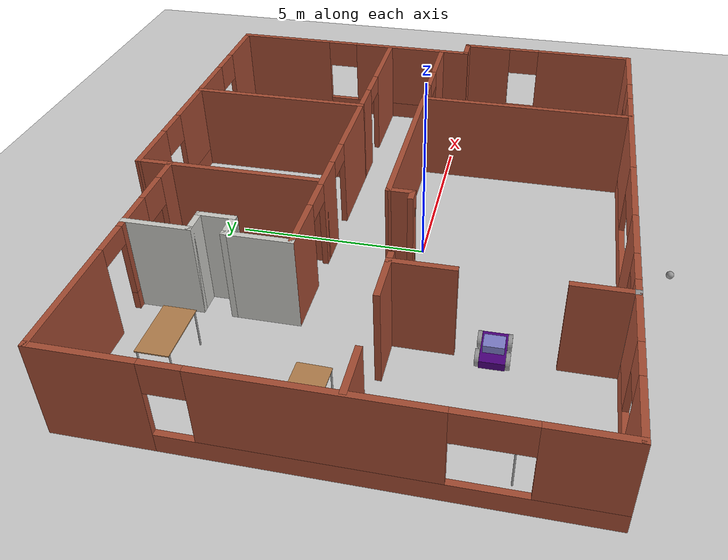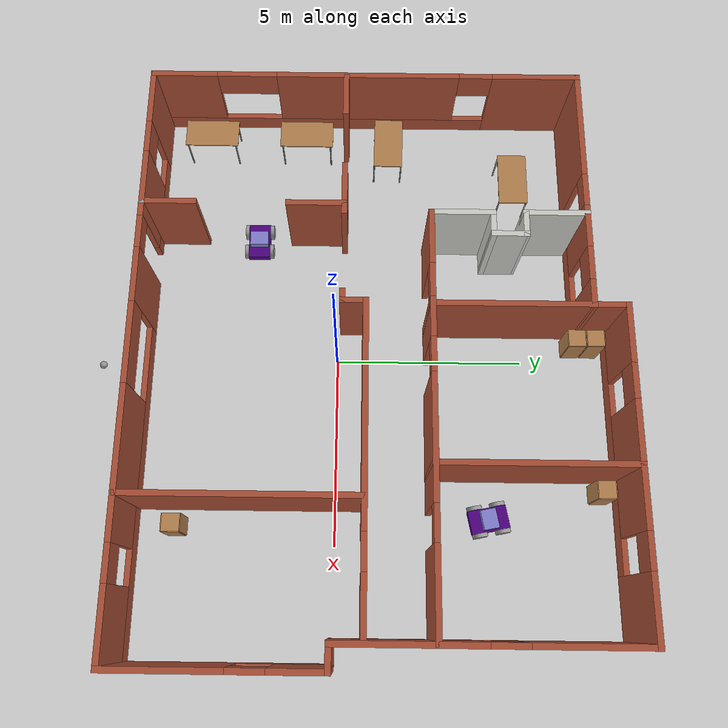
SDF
<sdf version="1.6">
 <world name="default">
  <light name="sun" type="directional">
   <pose>0 0 10 0 -0 0</pose>
   <diffuse>0.8 0.8 0.8 1</diffuse>
   <specular>0.2 0.2 0.2 1</specular>
   <attenuation>
    <range>1000</range>
    <constant>0.9</constant>
    <linear>0.01</linear>
    <quadratic>0.001</quadratic>
   </attenuation>
   <direction>-0.5 0.1 -0.9</direction>
   <spot><inner_angle>0</inner_angle><outer_angle>0</outer_angle><falloff>0</falloff></spot>
  </light>
  <model name="ground_plane">
   <static>1</static>
   <link name="link_gp">
    <collision name="collision">
     <geometry><plane><normal>0 0 1</normal><size>100 100</size></plane></geometry>
     <surface>
      <contact><collide_bitmask>65535</collide_bitmask></contact>
      <friction><ode><mu>100</mu><mu2>50</mu2></ode></friction>
     </surface>
    </collision>
    <visual name="visual">
     <cast_shadows>0</cast_shadows>
     <geometry><plane><normal>0 0 1</normal><size>100 100</size></plane></geometry>
     <material>
      <script><uri>file://media/materials/scripts/gazebo.material</uri><name>Gazebo/Grey</name></script>
     </material>
    </visual>
   </link>
  </model>
  <gravity>0 0 -9.8</gravity>
  <magnetic_field>6e-06 2.3e-05 -4.2e-05</magnetic_field>
  <atmosphere type="adiabatic"/>
  <physics name="default_physics" default="0" type="ode">
   <max_step_size>0.001</max_step_size>
   <real_time_factor>1</real_time_factor>
   <real_time_update_rate>1000</real_time_update_rate>
  </physics>
  <scene><ambient>0.4 0.4 0.4 1</ambient><background>0.7 0.7 0.7 1</background><shadows>1</shadows></scene>
  <audio><device>default</device></audio>
  <spherical_coordinates>
   <surface_model>EARTH_WGS84</surface_model>
   <latitude_deg>0</latitude_deg>
   <longitude_deg>0</longitude_deg>
   <elevation>0</elevation>
   <heading_deg>0</heading_deg>
  </spherical_coordinates>
  <model name="Building_0">
   <pose>0.213868 1.09211 0 0 -0 0</pose>
   <link name="Wall_0">
    <pose>0 -6.22497 0 0 -0 1.8e-05</pose>
    <visual name="Wall_0_Visual_0">
     <pose>-6.95411 0 1.25 0 -0 0</pose>
     <geometry><box><size>1.59152 0.15 2.5</size></box></geometry>
     <material>
      <script><uri>file://media/materials/scripts/gazebo.material</uri><name>Gazebo/Bricks</name></script>
      <ambient>0.996078 0.47451 0.0196078 1</ambient>
     </material>
     <meta><layer>0</layer></meta>
    </visual>
    <collision name="Wall_0_Collision_0">
     <geometry><box><size>1.59152 0.15 2.5</size></box></geometry>
     <pose>-6.95411 0 1.25 0 -0 0</pose>
    </collision>
    <visual name="Wall_0_Visual_1">
     <pose>-1.72012 0 1.25 0 -0 0</pose>
     <geometry><box><size>1.46885 0.15 2.5</size></box></geometry>
     <material>
      <script><uri>file://media/materials/scripts/gazebo.material</uri><name>Gazebo/Bricks</name></script>
      <ambient>0.996078 0.47451 0.0196078 1</ambient>
     </material>
     <meta><layer>0</layer></meta>
    </visual>
    <collision name="Wall_0_Collision_1">
     <geometry><box><size>1.46885 0.15 2.5</size></box></geometry>
     <pose>-1.72012 0 1.25 0 -0 0</pose>
    </collision>
    <visual name="Wall_0_Visual_2">
     <pose>-4.75645 0 0.25 0 -0 0</pose>
     <geometry><box><size>2.8038 0.15 0.5</size></box></geometry>
     <material>
      <script><uri>file://media/materials/scripts/gazebo.material</uri><name>Gazebo/Bricks</name></script>
      <ambient>0.996078 0.47451 0.0196078 1</ambient>
     </material>
     <meta><layer>0</layer></meta>
    </visual>
    <collision name="Wall_0_Collision_2">
     <geometry><box><size>2.8038 0.15 0.5</size></box></geometry>
     <pose>-4.75645 0 0.25 0 -0 0</pose>
    </collision>
    <visual name="Wall_0_Visual_3">
     <pose>3.38209 0 0.25 0 -0 0</pose>
     <geometry><box><size>8.73556 0.15 0.5</size></box></geometry>
     <material>
      <script><uri>file://media/materials/scripts/gazebo.material</uri><name>Gazebo/Bricks</name></script>
      <ambient>0.996078 0.47451 0.0196078 1</ambient>
     </material>
     <meta><layer>0</layer></meta>
    </visual>
    <collision name="Wall_0_Collision_3">
     <geometry><box><size>8.73556 0.15 0.5</size></box></geometry>
     <pose>3.38209 0 0.25 0 -0 0</pose>
    </collision>
    <visual name="Wall_0_Visual_4">
     <pose>-4.30145 0 1.5 0 -0 0</pose>
     <geometry><box><size>1.8938 0.15 2</size></box></geometry>
     <material>
      <script><uri>file://media/materials/scripts/gazebo.material</uri><name>Gazebo/Bricks</name></script>
      <ambient>0.996078 0.47451 0.0196078 1</ambient>
     </material>
     <meta><layer>0</layer></meta>
    </visual>
    <collision name="Wall_0_Collision_4">
     <geometry><box><size>1.8938 0.15 2</size></box></geometry>
     <pose>-4.30145 0 1.5 0 -0 0</pose>
    </collision>
    <visual name="Wall_0_Visual_5">
     <pose>-4.30145 0 1.5 0 -0 0</pose>
     <geometry><box><size>1.8938 0.15 2</size></box></geometry>
     <material>
      <script><uri>file://media/materials/scripts/gazebo.material</uri><name>Gazebo/Bricks</name></script>
      <ambient>0.996078 0.47451 0.0196078 1</ambient>
     </material>
     <meta><layer>0</layer></meta>
    </visual>
    <collision name="Wall_0_Collision_5">
     <geometry><box><size>1.8938 0.15 2</size></box></geometry>
     <pose>-4.30145 0 1.5 0 -0 0</pose>
    </collision>
    <visual name="Wall_0_Visual_6">
     <pose>3.04432 0 1.5 0 -0 0</pose>
     <geometry><box><size>3.80004 0.15 2</size></box></geometry>
     <material>
      <script><uri>file://media/materials/scripts/gazebo.material</uri><name>Gazebo/Bricks</name></script>
      <ambient>0.996078 0.47451 0.0196078 1</ambient>
     </material>
     <meta><layer>0</layer></meta>
    </visual>
    <collision name="Wall_0_Collision_6">
     <geometry><box><size>3.80004 0.15 2</size></box></geometry>
     <pose>3.04432 0 1.5 0 -0 0</pose>
    </collision>
    <visual name="Wall_0_Visual_7">
     <pose>6.80211 0 1.5 0 -0 0</pose>
     <geometry><box><size>1.89552 0.15 2</size></box></geometry>
     <material>
      <script><uri>file://media/materials/scripts/gazebo.material</uri><name>Gazebo/Bricks</name></script>
      <ambient>0.996078 0.47451 0.0196078 1</ambient>
     </material>
     <meta><layer>0</layer></meta>
    </visual>
    <collision name="Wall_0_Collision_7">
     <geometry><box><size>1.89552 0.15 2</size></box></geometry>
     <pose>6.80211 0 1.5 0 -0 0</pose>
    </collision>
    <visual name="Wall_0_Visual_8">
     <pose>-5.70335 0 2.1 0 -0 0</pose>
     <geometry><box><size>0.91 0.15 0.8</size></box></geometry>
     <material>
      <script><uri>file://media/materials/scripts/gazebo.material</uri><name>Gazebo/Bricks</name></script>
      <ambient>0.996078 0.47451 0.0196078 1</ambient>
     </material>
     <meta><layer>0</layer></meta>
    </visual>
    <collision name="Wall_0_Collision_8">
     <geometry><box><size>0.91 0.15 0.8</size></box></geometry>
     <pose>-5.70335 0 2.1 0 -0 0</pose>
    </collision>
    <visual name="Wall_0_Visual_9">
     <pose>0.079304 0 2.1 0 -0 0</pose>
     <geometry><box><size>2.13 0.15 0.8</size></box></geometry>
     <material>
      <script><uri>file://media/materials/scripts/gazebo.material</uri><name>Gazebo/Bricks</name></script>
      <ambient>0.996078 0.47451 0.0196078 1</ambient>
     </material>
     <meta><layer>0</layer></meta>
    </visual>
    <collision name="Wall_0_Collision_9">
     <geometry><box><size>2.13 0.15 0.8</size></box></geometry>
     <pose>0.079304 0 2.1 0 -0 0</pose>
    </collision>
    <visual name="Wall_0_Visual_10">
     <pose>5.39934 0 2.1 0 -0 0</pose>
     <geometry><box><size>0.91 0.15 0.8</size></box></geometry>
     <material>
      <script><uri>file://media/materials/scripts/gazebo.material</uri><name>Gazebo/Bricks</name></script>
      <ambient>0.996078 0.47451 0.0196078 1</ambient>
     </material>
     <meta><layer>0</layer></meta>
    </visual>
    <collision name="Wall_0_Collision_10">
     <geometry><box><size>0.91 0.15 0.8</size></box></geometry>
     <pose>5.39934 0 2.1 0 -0 0</pose>
    </collision>
    <visual name="Wall_0_Visual_11">
     <pose>-2.90454 0 2.25 0 -0 0</pose>
     <geometry><box><size>0.9 0.15 0.5</size></box></geometry>
     <material>
      <script><uri>file://media/materials/scripts/gazebo.material</uri><name>Gazebo/Bricks</name></script>
      <ambient>0.996078 0.47451 0.0196078 1</ambient>
     </material>
     <meta><layer>0</layer></meta>
    </visual>
    <collision name="Wall_0_Collision_11">
     <geometry><box><size>0.9 0.15 0.5</size></box></geometry>
     <pose>-2.90454 0 2.25 0 -0 0</pose>
    </collision>
    <visual name="Wall_0_Visual_12">
     <pose>-2.90454 0 2.25 0 -0 0</pose>
     <geometry><box><size>0.9 0.15 0.5</size></box></geometry>
     <material>
      <script><uri>file://media/materials/scripts/gazebo.material</uri><name>Gazebo/Bricks</name></script>
      <ambient>0.996078 0.47451 0.0196078 1</ambient>
     </material>
     <meta><layer>0</layer></meta>
    </visual>
    <collision name="Wall_0_Collision_12">
     <geometry><box><size>0.9 0.15 0.5</size></box></geometry>
     <pose>-2.90454 0 2.25 0 -0 0</pose>
    </collision>
   </link>
   <link name="Wall_1">
    <pose>7.67487 -3.67484 0 0 -0 1.5708</pose>
    <visual name="Wall_1_Visual_0">
     <pose>-1.17636 0 1.25 0 -0 0</pose>
     <geometry><box><size>2.89728 0.15 2.5</size></box></geometry>
     <material>
      <script><uri>file://media/materials/scripts/gazebo.material</uri><name>Gazebo/Bricks</name></script>
      <ambient>0.996078 0.47451 0.0196078 1</ambient>
     </material>
     <meta><layer>0</layer></meta>
    </visual>
    <collision name="Wall_1_Collision_0">
     <geometry><box><size>2.89728 0.15 2.5</size></box></geometry>
     <pose>-1.17636 0 1.25 0 -0 0</pose>
    </collision>
    <visual name="Wall_1_Visual_1">
     <pose>1.44864 0 0.25 0 -0 0</pose>
     <geometry><box><size>2.35272 0.15 0.5</size></box></geometry>
     <material>
      <script><uri>file://media/materials/scripts/gazebo.material</uri><name>Gazebo/Bricks</name></script>
      <ambient>0.996078 0.47451 0.0196078 1</ambient>
     </material>
     <meta><layer>0</layer></meta>
    </visual>
    <collision name="Wall_1_Collision_1">
     <geometry><box><size>2.35272 0.15 0.5</size></box></geometry>
     <pose>1.44864 0 0.25 0 -0 0</pose>
    </collision>
    <visual name="Wall_1_Visual_2">
     <pose>1.90364 0 1.5 0 -0 0</pose>
     <geometry><box><size>1.44272 0.15 2</size></box></geometry>
     <material>
      <script><uri>file://media/materials/scripts/gazebo.material</uri><name>Gazebo/Bricks</name></script>
      <ambient>0.996078 0.47451 0.0196078 1</ambient>
     </material>
     <meta><layer>0</layer></meta>
    </visual>
    <collision name="Wall_1_Collision_2">
     <geometry><box><size>1.44272 0.15 2</size></box></geometry>
     <pose>1.90364 0 1.5 0 -0 0</pose>
    </collision>
    <visual name="Wall_1_Visual_3">
     <pose>0.727284 0 2.1 0 -0 0</pose>
     <geometry><box><size>0.91 0.15 0.8</size></box></geometry>
     <material>
      <script><uri>file://media/materials/scripts/gazebo.material</uri><name>Gazebo/Bricks</name></script>
      <ambient>0.996078 0.47451 0.0196078 1</ambient>
     </material>
     <meta><layer>0</layer></meta>
    </visual>
    <collision name="Wall_1_Collision_3">
     <geometry><box><size>0.91 0.15 0.8</size></box></geometry>
     <pose>0.727284 0 2.1 0 -0 0</pose>
    </collision>
   </link>
   <link name="Wall_10">
    <collision name="Wall_10_Collision">
     <geometry><box><size>0.75 0.15 2.5</size></box></geometry>
     <pose>0 0 1.25 0 -0 0</pose>
    </collision>
    <visual name="Wall_10_Visual">
     <pose>0 0 1.25 0 -0 0</pose>
     <geometry><box><size>0.75 0.15 2.5</size></box></geometry>
     <material>
      <script><uri>file://media/materials/scripts/gazebo.material</uri><name>Gazebo/Bricks</name></script>
      <ambient>1 1 1 1</ambient>
     </material>
     <meta><layer>0</layer></meta>
    </visual>
    <pose>-1.075 -0.651084 0 0 -0 1.57124</pose>
   </link>
   <link name="Wall_11">
    <pose>2.97487 -0.351058 0 0 -0 0</pose>
    <visual name="Wall_11_Visual_0">
     <pose>-1.23718 0 1.25 0 -0 0</pose>
     <geometry><box><size>5.77565 0.15 2.5</size></box></geometry>
     <material>
      <script><uri>file://media/materials/scripts/gazebo.material</uri><name>Gazebo/Bricks</name></script>
      <ambient>1 1 1 1</ambient>
     </material>
     <meta><layer>0</layer></meta>
    </visual>
    <collision name="Wall_11_Collision_0">
     <geometry><box><size>5.77565 0.15 2.5</size></box></geometry>
     <pose>-1.23718 0 1.25 0 -0 0</pose>
    </collision>
    <visual name="Wall_11_Visual_1">
     <pose>3.33782 0 1.25 0 -0 0</pose>
     <geometry><box><size>1.57435 0.15 2.5</size></box></geometry>
     <material>
      <script><uri>file://media/materials/scripts/gazebo.material</uri><name>Gazebo/Bricks</name></script>
      <ambient>1 1 1 1</ambient>
     </material>
     <meta><layer>0</layer></meta>
    </visual>
    <collision name="Wall_11_Collision_1">
     <geometry><box><size>1.57435 0.15 2.5</size></box></geometry>
     <pose>3.33782 0 1.25 0 -0 0</pose>
    </collision>
    <visual name="Wall_11_Visual_2">
     <pose>2.10065 0 2.25 0 -0 0</pose>
     <geometry><box><size>0.9 0.15 0.5</size></box></geometry>
     <material>
      <script><uri>file://media/materials/scripts/gazebo.material</uri><name>Gazebo/Bricks</name></script>
      <ambient>1 1 1 1</ambient>
     </material>
     <meta><layer>0</layer></meta>
    </visual>
    <collision name="Wall_11_Collision_2">
     <geometry><box><size>0.9 0.15 0.5</size></box></geometry>
     <pose>2.10065 0 2.25 0 -0 0</pose>
    </collision>
   </link>
   <link name="Wall_18">
    <pose>7.07487 2.55016 0 0 -0 -1.5708</pose>
    <visual name="Wall_18_Visual_0">
     <pose>-2.28748 0 1.25 0 -0 0</pose>
     <geometry><box><size>2.92503 0.15 2.5</size></box></geometry>
     <material>
      <script><uri>file://media/materials/scripts/gazebo.material</uri><name>Gazebo/Bricks</name></script>
      <ambient>0.996078 0.47451 0.0196078 1</ambient>
     </material>
     <meta><layer>0</layer></meta>
    </visual>
    <collision name="Wall_18_Collision_0">
     <geometry><box><size>2.92503 0.15 2.5</size></box></geometry>
     <pose>-2.28748 0 1.25 0 -0 0</pose>
    </collision>
    <visual name="Wall_18_Visual_1">
     <pose>1.46252 0 0.25 0 -0 0</pose>
     <geometry><box><size>4.57497 0.15 0.5</size></box></geometry>
     <material>
      <script><uri>file://media/materials/scripts/gazebo.material</uri><name>Gazebo/Bricks</name></script>
      <ambient>0.996078 0.47451 0.0196078 1</ambient>
     </material>
     <meta><layer>0</layer></meta>
    </visual>
    <collision name="Wall_18_Collision_1">
     <geometry><box><size>4.57497 0.15 0.5</size></box></geometry>
     <pose>1.46252 0 0.25 0 -0 0</pose>
    </collision>
    <visual name="Wall_18_Visual_2">
     <pose>1.91752 0 1.5 0 -0 0</pose>
     <geometry><box><size>3.66497 0.15 2</size></box></geometry>
     <material>
      <script><uri>file://media/materials/scripts/gazebo.material</uri><name>Gazebo/Bricks</name></script>
      <ambient>0.996078 0.47451 0.0196078 1</ambient>
     </material>
     <meta><layer>0</layer></meta>
    </visual>
    <collision name="Wall_18_Collision_2">
     <geometry><box><size>3.66497 0.15 2</size></box></geometry>
     <pose>1.91752 0 1.5 0 -0 0</pose>
    </collision>
    <visual name="Wall_18_Visual_3">
     <pose>-0.369968 0 2.1 0 -0 0</pose>
     <geometry><box><size>0.91 0.15 0.8</size></box></geometry>
     <material>
      <script><uri>file://media/materials/scripts/gazebo.material</uri><name>Gazebo/Bricks</name></script>
      <ambient>0.996078 0.47451 0.0196078 1</ambient>
     </material>
     <meta><layer>0</layer></meta>
    </visual>
    <collision name="Wall_18_Collision_3">
     <geometry><box><size>0.91 0.15 0.8</size></box></geometry>
     <pose>-0.369968 0 2.1 0 -0 0</pose>
    </collision>
   </link>
   <link name="Wall_2">
    <collision name="Wall_2_Collision">
     <geometry><box><size>0.75 0.15 2.5</size></box></geometry>
     <pose>0 0 1.25 0 -0 0</pose>
    </collision>
    <visual name="Wall_2_Visual">
     <pose>0 0 1.25 0 -0 0</pose>
     <geometry><box><size>0.75 0.15 2.5</size></box></geometry>
     <material>
      <script><uri>file://media/materials/scripts/gazebo.material</uri><name>Gazebo/Bricks</name></script>
      <ambient>0.996078 0.47451 0.0196078 1</ambient>
     </material>
     <meta><layer>0</layer></meta>
    </visual>
    <pose>7.37487 -1.12484 0 0 -0 3.14159</pose>
   </link>
   <link name="Wall_20">
    <pose>1.74813 1.33189 0 0 -0 0</pose>
    <visual name="Wall_20_Visual_0">
     <pose>-4.61431 0 1.25 0 -0 0</pose>
     <geometry><box><size>1.52138 0.15 2.5</size></box></geometry>
     <material>
      <script><uri>file://media/materials/scripts/gazebo.material</uri><name>Gazebo/Bricks</name></script>
      <ambient>1 1 1 1</ambient>
     </material>
     <meta><layer>0</layer></meta>
    </visual>
    <collision name="Wall_20_Collision_0">
     <geometry><box><size>1.52138 0.15 2.5</size></box></geometry>
     <pose>-4.61431 0 1.25 0 -0 0</pose>
    </collision>
    <visual name="Wall_20_Visual_1">
     <pose>-2.42081 0 1.25 0 -0 0</pose>
     <geometry><box><size>1.06562 0.15 2.5</size></box></geometry>
     <material>
      <script><uri>file://media/materials/scripts/gazebo.material</uri><name>Gazebo/Bricks</name></script>
      <ambient>1 1 1 1</ambient>
     </material>
     <meta><layer>0</layer></meta>
    </visual>
    <collision name="Wall_20_Collision_1">
     <geometry><box><size>1.06562 0.15 2.5</size></box></geometry>
     <pose>-2.42081 0 1.25 0 -0 0</pose>
    </collision>
    <visual name="Wall_20_Visual_2">
     <pose>0.609298 0 1.25 0 -0 0</pose>
     <geometry><box><size>3.1946 0.15 2.5</size></box></geometry>
     <material>
      <script><uri>file://media/materials/scripts/gazebo.material</uri><name>Gazebo/Bricks</name></script>
      <ambient>1 1 1 1</ambient>
     </material>
     <meta><layer>0</layer></meta>
    </visual>
    <collision name="Wall_20_Collision_2">
     <geometry><box><size>3.1946 0.15 2.5</size></box></geometry>
     <pose>0.609298 0 1.25 0 -0 0</pose>
    </collision>
    <visual name="Wall_20_Visual_3">
     <pose>4.2408 0 1.25 0 -0 0</pose>
     <geometry><box><size>2.2684 0.15 2.5</size></box></geometry>
     <material>
      <script><uri>file://media/materials/scripts/gazebo.material</uri><name>Gazebo/Bricks</name></script>
      <ambient>1 1 1 1</ambient>
     </material>
     <meta><layer>0</layer></meta>
    </visual>
    <collision name="Wall_20_Collision_3">
     <geometry><box><size>2.2684 0.15 2.5</size></box></geometry>
     <pose>4.2408 0 1.25 0 -0 0</pose>
    </collision>
    <visual name="Wall_20_Visual_4">
     <pose>-3.40362 0 2.25 0 -0 0</pose>
     <geometry><box><size>0.9 0.15 0.5</size></box></geometry>
     <material>
      <script><uri>file://media/materials/scripts/gazebo.material</uri><name>Gazebo/Bricks</name></script>
      <ambient>1 1 1 1</ambient>
     </material>
     <meta><layer>0</layer></meta>
    </visual>
    <collision name="Wall_20_Collision_4">
     <geometry><box><size>0.9 0.15 0.5</size></box></geometry>
     <pose>-3.40362 0 2.25 0 -0 0</pose>
    </collision>
    <visual name="Wall_20_Visual_5">
     <pose>-1.438 0 2.25 0 -0 0</pose>
     <geometry><box><size>0.9 0.15 0.5</size></box></geometry>
     <material>
      <script><uri>file://media/materials/scripts/gazebo.material</uri><name>Gazebo/Bricks</name></script>
      <ambient>1 1 1 1</ambient>
     </material>
     <meta><layer>0</layer></meta>
    </visual>
    <collision name="Wall_20_Collision_5">
     <geometry><box><size>0.9 0.15 0.5</size></box></geometry>
     <pose>-1.438 0 2.25 0 -0 0</pose>
    </collision>
    <visual name="Wall_20_Visual_6">
     <pose>2.6566 0 2.25 0 -0 0</pose>
     <geometry><box><size>0.9 0.15 0.5</size></box></geometry>
     <material>
      <script><uri>file://media/materials/scripts/gazebo.material</uri><name>Gazebo/Bricks</name></script>
      <ambient>1 1 1 1</ambient>
     </material>
     <meta><layer>0</layer></meta>
    </visual>
    <collision name="Wall_20_Collision_6">
     <geometry><box><size>0.9 0.15 0.5</size></box></geometry>
     <pose>2.6566 0 2.25 0 -0 0</pose>
    </collision>
   </link>
   <link name="Wall_22">
    <collision name="Wall_22_Collision">
     <geometry><box><size>1.75 0.15 2.5</size></box></geometry>
     <pose>0 0 1.25 0 -0 0</pose>
    </collision>
    <visual name="Wall_22_Visual">
     <pose>0 0 1.25 0 -0 0</pose>
     <geometry><box><size>1.75 0.15 2.5</size></box></geometry>
     <material>
      <script><uri>file://media/materials/scripts/gazebo.material</uri><name>Gazebo/CeilingTiled</name></script>
      <ambient>0.435294 0.796078 0.67451 1</ambient>
     </material>
     <meta><layer>0</layer></meta>
    </visual>
    <pose>-3.5522 4.57947 0 0 -0 -1.5708</pose>
   </link>
   <link name="Wall_26">
    <collision name="Wall_26_Collision">
     <geometry><box><size>1.74786 0.15 2.5</size></box></geometry>
     <pose>0 0 1.25 0 -0 0</pose>
    </collision>
    <visual name="Wall_26_Visual">
     <pose>0 0 1.25 0 -0 0</pose>
     <geometry><box><size>1.74786 0.15 2.5</size></box></geometry>
     <material>
      <script><uri>file://media/materials/scripts/gazebo.material</uri><name>Gazebo/CeilingTiled</name></script>
      <ambient>0.435294 0.796078 0.67451 1</ambient>
     </material>
     <meta><layer>0</layer></meta>
    </visual>
    <pose>-3.55187 2.13089 0 0 -0 -1.5708</pose>
   </link>
   <link name="Wall_28">
    <collision name="Wall_28_Collision">
     <geometry><box><size>0.75 0.15 2.5</size></box></geometry>
     <pose>0 0 1.25 0 -0 0</pose>
    </collision>
    <visual name="Wall_28_Visual">
     <pose>0 0 1.25 0 -0 0</pose>
     <geometry><box><size>0.75 0.15 2.5</size></box></geometry>
     <material>
      <script><uri>file://media/materials/scripts/gazebo.material</uri><name>Gazebo/CeilingTiled</name></script>
      <ambient>0.435294 0.796078 0.67451 1</ambient>
     </material>
     <meta><layer>0</layer></meta>
    </visual>
    <pose>-3.2522 3.77947 0 0 -0 0</pose>
   </link>
   <link name="Wall_29">
    <collision name="Wall_29_Collision">
     <geometry><box><size>0.999577 0.15 2.5</size></box></geometry>
     <pose>0 0 1.25 0 -0 0</pose>
    </collision>
    <visual name="Wall_29_Visual">
     <pose>0 0 1.25 0 -0 0</pose>
     <geometry><box><size>0.999577 0.15 2.5</size></box></geometry>
     <material>
      <script><uri>file://media/materials/scripts/gazebo.material</uri><name>Gazebo/CeilingTiled</name></script>
      <ambient>0.435294 0.796078 0.67451 1</ambient>
     </material>
     <meta><layer>0</layer></meta>
    </visual>
    <pose>-2.95203 3.35468 0 0 -0 -1.5704</pose>
   </link>
   <link name="Wall_30">
    <collision name="Wall_30_Collision">
     <geometry><box><size>0.750333 0.15 2.5</size></box></geometry>
     <pose>0 0 1.25 0 -0 0</pose>
    </collision>
    <visual name="Wall_30_Visual">
     <pose>0 0 1.25 0 -0 0</pose>
     <geometry><box><size>0.750333 0.15 2.5</size></box></geometry>
     <material>
      <script><uri>file://media/materials/scripts/gazebo.material</uri><name>Gazebo/CeilingTiled</name></script>
      <ambient>0.435294 0.796078 0.67451 1</ambient>
     </material>
     <meta><layer>0</layer></meta>
    </visual>
    <pose>-3.25187 2.92989 0 0 -0 3.14159</pose>
   </link>
   <link name="Wall_32">
    <collision name="Wall_32_Collision">
     <geometry><box><size>4.193 0.15 2.5</size></box></geometry>
     <pose>0 0 1.25 0 -0 0</pose>
    </collision>
    <visual name="Wall_32_Visual">
     <pose>0 0 1.25 0 -0 0</pose>
     <geometry><box><size>4.193 0.15 2.5</size></box></geometry>
     <material>
      <script><uri>file://media/materials/scripts/gazebo.material</uri><name>Gazebo/Bricks</name></script>
      <ambient>1 1 1 1</ambient>
     </material>
     <meta><layer>0</layer></meta>
    </visual>
    <pose>-1.02487 3.35339 0 0 -0 -1.5708</pose>
   </link>
   <link name="Wall_34">
    <collision name="Wall_34_Collision">
     <geometry><box><size>5.043 0.15 2.5</size></box></geometry>
     <pose>0 0 1.25 0 -0 0</pose>
    </collision>
    <visual name="Wall_34_Visual">
     <pose>0 0 1.25 0 -0 0</pose>
     <geometry><box><size>5.043 0.15 2.5</size></box></geometry>
     <material>
      <script><uri>file://media/materials/scripts/gazebo.material</uri><name>Gazebo/Bricks</name></script>
      <ambient>1 1 1 1</ambient>
     </material>
     <meta><layer>0</layer></meta>
    </visual>
    <pose>2.99413 3.77839 0 0 -0 -1.5708</pose>
   </link>
   <link name="Wall_38">
    <collision name="Wall_38_Collision">
     <geometry><box><size>5.98268 0.15 2.5</size></box></geometry>
     <pose>0 0 1.25 0 -0 0</pose>
    </collision>
    <visual name="Wall_38_Visual">
     <pose>0 0 1.25 0 -0 0</pose>
     <geometry><box><size>5.98268 0.15 2.5</size></box></geometry>
     <material>
      <script><uri>file://media/materials/scripts/gazebo.material</uri><name>Gazebo/Bricks</name></script>
      <ambient>1 1 1 1</ambient>
     </material>
     <meta><layer>0</layer></meta>
    </visual>
    <pose>3.80313 -3.26761 0 0 -0 -1.5708</pose>
   </link>
   <link name="Wall_4">
    <pose>3.02487 6.22516 0 0 -0 3.14159</pose>
    <visual name="Wall_4_Visual_0">
     <pose>-3.26906 0 1.25 0 -0 0</pose>
     <geometry><box><size>1.71187 0.15 2.5</size></box></geometry>
     <material>
      <script><uri>file://media/materials/scripts/gazebo.material</uri><name>Gazebo/Bricks</name></script>
      <ambient>0.996078 0.47451 0.0196078 1</ambient>
     </material>
     <meta><layer>0</layer></meta>
    </visual>
    <collision name="Wall_4_Collision_0">
     <geometry><box><size>1.71187 0.15 2.5</size></box></geometry>
     <pose>-3.26906 0 1.25 0 -0 0</pose>
    </collision>
    <visual name="Wall_4_Visual_1">
     <pose>0.855937 0 0.25 0 -0 0</pose>
     <geometry><box><size>6.53813 0.15 0.5</size></box></geometry>
     <material>
      <script><uri>file://media/materials/scripts/gazebo.material</uri><name>Gazebo/Bricks</name></script>
      <ambient>0.996078 0.47451 0.0196078 1</ambient>
     </material>
     <meta><layer>0</layer></meta>
    </visual>
    <collision name="Wall_4_Collision_1">
     <geometry><box><size>6.53813 0.15 0.5</size></box></geometry>
     <pose>0.855937 0 0.25 0 -0 0</pose>
    </collision>
    <visual name="Wall_4_Visual_2">
     <pose>0.065803 0 1.5 0 -0 0</pose>
     <geometry><box><size>3.13786 0.15 2</size></box></geometry>
     <material>
      <script><uri>file://media/materials/scripts/gazebo.material</uri><name>Gazebo/Bricks</name></script>
      <ambient>0.996078 0.47451 0.0196078 1</ambient>
     </material>
     <meta><layer>0</layer></meta>
    </visual>
    <collision name="Wall_4_Collision_2">
     <geometry><box><size>3.13786 0.15 2</size></box></geometry>
     <pose>0.065803 0 1.5 0 -0 0</pose>
    </collision>
    <visual name="Wall_4_Visual_3">
     <pose>3.33487 0 1.5 0 -0 0</pose>
     <geometry><box><size>1.58027 0.15 2</size></box></geometry>
     <material>
      <script><uri>file://media/materials/scripts/gazebo.material</uri><name>Gazebo/Bricks</name></script>
      <ambient>0.996078 0.47451 0.0196078 1</ambient>
     </material>
     <meta><layer>0</layer></meta>
    </visual>
    <collision name="Wall_4_Collision_3">
     <geometry><box><size>1.58027 0.15 2</size></box></geometry>
     <pose>3.33487 0 1.5 0 -0 0</pose>
    </collision>
    <visual name="Wall_4_Visual_4">
     <pose>-1.95813 0 2.1 0 -0 0</pose>
     <geometry><box><size>0.91 0.15 0.8</size></box></geometry>
     <material>
      <script><uri>file://media/materials/scripts/gazebo.material</uri><name>Gazebo/Bricks</name></script>
      <ambient>0.996078 0.47451 0.0196078 1</ambient>
     </material>
     <meta><layer>0</layer></meta>
    </visual>
    <collision name="Wall_4_Collision_4">
     <geometry><box><size>0.91 0.15 0.8</size></box></geometry>
     <pose>-1.95813 0 2.1 0 -0 0</pose>
    </collision>
    <visual name="Wall_4_Visual_5">
     <pose>2.08973 0 2.1 0 -0 0</pose>
     <geometry><box><size>0.91 0.15 0.8</size></box></geometry>
     <material>
      <script><uri>file://media/materials/scripts/gazebo.material</uri><name>Gazebo/Bricks</name></script>
      <ambient>0.996078 0.47451 0.0196078 1</ambient>
     </material>
     <meta><layer>0</layer></meta>
    </visual>
    <collision name="Wall_4_Collision_5">
     <geometry><box><size>0.91 0.15 0.8</size></box></geometry>
     <pose>2.08973 0 2.1 0 -0 0</pose>
    </collision>
   </link>
   <link name="Wall_43">
    <collision name="Wall_43_Collision">
     <geometry><box><size>1.25 0.15 2.5</size></box></geometry>
     <pose>0 0 1.25 0 -0 0</pose>
    </collision>
    <visual name="Wall_43_Visual">
     <pose>0 0 1.25 0 -0 0</pose>
     <geometry><box><size>1.25 0.15 2.5</size></box></geometry>
     <material>
      <script><uri>file://media/materials/scripts/gazebo.material</uri><name>Gazebo/Bricks</name></script>
      <ambient>1 1 1 1</ambient>
     </material>
     <meta><layer>0</layer></meta>
    </visual>
    <pose>-7.07319 -0.935189 0 0 -0 0</pose>
   </link>
   <link name="Wall_45">
    <collision name="Wall_45_Collision">
     <geometry><box><size>1.5 0.15 2.5</size></box></geometry>
     <pose>0 0 1.25 0 -0 0</pose>
    </collision>
    <visual name="Wall_45_Visual">
     <pose>0 0 1.25 0 -0 0</pose>
     <geometry><box><size>1.5 0.15 2.5</size></box></geometry>
     <material>
      <script><uri>file://media/materials/scripts/gazebo.material</uri><name>Gazebo/Bricks</name></script>
      <ambient>1 1 1 1</ambient>
     </material>
     <meta><layer>0</layer></meta>
    </visual>
    <pose>-4.21878 -0.935189 0 0 -0 0</pose>
   </link>
   <link name="Wall_47">
    <collision name="Wall_47_Collision">
     <geometry><box><size>0.383939 0.15 2.5</size></box></geometry>
     <pose>0 0 1.25 0 -0 0</pose>
    </collision>
    <visual name="Wall_47_Visual">
     <pose>0 0 1.25 0 -0 0</pose>
     <geometry><box><size>0.383939 0.15 2.5</size></box></geometry>
     <material>
      <script><uri>file://media/materials/scripts/gazebo.material</uri><name>Gazebo/Bricks</name></script>
      <ambient>1 1 1 1</ambient>
     </material>
     <meta><layer>0</layer></meta>
    </visual>
    <pose>-1.19187 -0.95111 0 0 -0 0</pose>
   </link>
   <link name="Wall_49">
    <collision name="Wall_49_Collision">
     <geometry><box><size>0.16 0.15 2.5</size></box></geometry>
     <pose>0 0 1.25 0 -0 0</pose>
    </collision>
    <visual name="Wall_49_Visual">
     <pose>0 0 1.25 0 -0 0</pose>
     <geometry><box><size>0.16 0.15 2.5</size></box></geometry>
     <material>
      <script><uri>file://media/materials/scripts/gazebo.material</uri><name>Gazebo/Grey</name></script>
      <ambient>1 1 1 1</ambient>
     </material>
     <meta><layer>0</layer></meta>
    </visual>
    <pose>-3.78556 -6.22393 0 0 -0 0</pose>
   </link>
   <link name="Wall_5">
    <collision name="Wall_5_Collision">
     <geometry><box><size>1 0.15 2.5</size></box></geometry>
     <pose>0 0 1.25 0 -0 0</pose>
    </collision>
    <visual name="Wall_5_Visual">
     <pose>0 0 1.25 0 -0 0</pose>
     <geometry><box><size>1 0.15 2.5</size></box></geometry>
     <material>
      <script><uri>file://media/materials/scripts/gazebo.material</uri><name>Gazebo/Bricks</name></script>
      <ambient>1 1 1 1</ambient>
     </material>
     <meta><layer>0</layer></meta>
    </visual>
    <pose>-1.025 5.80003 0 0 -0 -1.57048</pose>
   </link>
   <link name="Wall_50">
    <collision name="Wall_50_Collision">
     <geometry><box><size>1.5 0.15 2.5</size></box></geometry>
     <pose>0 0 1.25 0 -0 0</pose>
    </collision>
    <visual name="Wall_50_Visual">
     <pose>0 0 1.25 0 -0 0</pose>
     <geometry><box><size>1.5 0.15 2.5</size></box></geometry>
     <material>
      <script><uri>file://media/materials/scripts/gazebo.material</uri><name>Gazebo/Bricks</name></script>
      <ambient>1 1 1 1</ambient>
     </material>
     <meta><layer>0</layer></meta>
    </visual>
    <pose>-3.78056 -5.54893 0 0 -0 1.5708</pose>
   </link>
   <link name="Wall_54">
    <collision name="Wall_54_Collision">
     <geometry><box><size>1.608 0.15 2.5</size></box></geometry>
     <pose>0 0 1.25 0 -0 0</pose>
    </collision>
    <visual name="Wall_54_Visual">
     <pose>0 0 1.25 0 -0 0</pose>
     <geometry><box><size>1.608 0.15 2.5</size></box></geometry>
     <material>
      <script><uri>file://media/materials/scripts/gazebo.material</uri><name>Gazebo/Bricks</name></script>
      <ambient>1 1 1 1</ambient>
     </material>
     <meta><layer>0</layer></meta>
    </visual>
    <pose>-3.77287 -1.66411 0 0 -0 1.5708</pose>
   </link>
   <link name="Wall_6">
    <pose>-4.34987 5.37489 0 0 -0 3.14159</pose>
    <visual name="Wall_6_Visual_0">
     <pose>-3.02019 0 1.25 0 -0 0</pose>
     <geometry><box><size>0.759364 0.15 2.5</size></box></geometry>
     <material>
      <script><uri>file://media/materials/scripts/gazebo.material</uri><name>Gazebo/Bricks</name></script>
      <ambient>0.996078 0.47451 0.0196078 1</ambient>
     </material>
     <meta><layer>0</layer></meta>
    </visual>
    <collision name="Wall_6_Collision_0">
     <geometry><box><size>0.759364 0.15 2.5</size></box></geometry>
     <pose>-3.02019 0 1.25 0 -0 0</pose>
    </collision>
    <visual name="Wall_6_Visual_1">
     <pose>1.87306 0 1.25 0 -0 0</pose>
     <geometry><box><size>3.05362 0.15 2.5</size></box></geometry>
     <material>
      <script><uri>file://media/materials/scripts/gazebo.material</uri><name>Gazebo/Bricks</name></script>
      <ambient>0.996078 0.47451 0.0196078 1</ambient>
     </material>
     <meta><layer>0</layer></meta>
    </visual>
    <collision name="Wall_6_Collision_1">
     <geometry><box><size>3.05362 0.15 2.5</size></box></geometry>
     <pose>1.87306 0 1.25 0 -0 0</pose>
    </collision>
    <visual name="Wall_6_Visual_2">
     <pose>-1.59713 0 0.25 0 -0 0</pose>
     <geometry><box><size>2.08676 0.15 0.5</size></box></geometry>
     <material>
      <script><uri>file://media/materials/scripts/gazebo.material</uri><name>Gazebo/Bricks</name></script>
      <ambient>0.996078 0.47451 0.0196078 1</ambient>
     </material>
     <meta><layer>0</layer></meta>
    </visual>
    <collision name="Wall_6_Collision_2">
     <geometry><box><size>2.08676 0.15 0.5</size></box></geometry>
     <pose>-1.59713 0 0.25 0 -0 0</pose>
    </collision>
    <visual name="Wall_6_Visual_3">
     <pose>-1.14213 0 1.5 0 -0 0</pose>
     <geometry><box><size>1.17675 0.15 2</size></box></geometry>
     <material>
      <script><uri>file://media/materials/scripts/gazebo.material</uri><name>Gazebo/Bricks</name></script>
      <ambient>0.996078 0.47451 0.0196078 1</ambient>
     </material>
     <meta><layer>0</layer></meta>
    </visual>
    <collision name="Wall_6_Collision_3">
     <geometry><box><size>1.17675 0.15 2</size></box></geometry>
     <pose>-1.14213 0 1.5 0 -0 0</pose>
    </collision>
    <visual name="Wall_6_Visual_4">
     <pose>-2.1855 0 2.1 0 -0 0</pose>
     <geometry><box><size>0.91 0.15 0.8</size></box></geometry>
     <material>
      <script><uri>file://media/materials/scripts/gazebo.material</uri><name>Gazebo/Bricks</name></script>
      <ambient>0.996078 0.47451 0.0196078 1</ambient>
     </material>
     <meta><layer>0</layer></meta>
    </visual>
    <collision name="Wall_6_Collision_4">
     <geometry><box><size>0.91 0.15 0.8</size></box></geometry>
     <pose>-2.1855 0 2.1 0 -0 0</pose>
    </collision>
    <visual name="Wall_6_Visual_5">
     <pose>-0.103749 0 2.25 0 -0 0</pose>
     <geometry><box><size>0.9 0.15 0.5</size></box></geometry>
     <material>
      <script><uri>file://media/materials/scripts/gazebo.material</uri><name>Gazebo/Bricks</name></script>
      <ambient>0.996078 0.47451 0.0196078 1</ambient>
     </material>
     <meta><layer>0</layer></meta>
    </visual>
    <collision name="Wall_6_Collision_5">
     <geometry><box><size>0.9 0.15 0.5</size></box></geometry>
     <pose>-0.103749 0 2.25 0 -0 0</pose>
    </collision>
   </link>
   <link name="Wall_7">
    <pose>-7.67487 -0.42511 0 0 -0 -1.5708</pose>
    <visual name="Wall_7_Visual_0">
     <pose>-4.67948 0 1.25 0 -0 0</pose>
     <geometry><box><size>2.39115 0.15 2.5</size></box></geometry>
     <material>
      <script><uri>file://media/materials/scripts/gazebo.material</uri><name>Gazebo/Bricks</name></script>
      <ambient>0.996078 0.47451 0.0196078 1</ambient>
     </material>
     <meta><layer>0</layer></meta>
    </visual>
    <collision name="Wall_7_Collision_0">
     <geometry><box><size>2.39115 0.15 2.5</size></box></geometry>
     <pose>-4.67948 0 1.25 0 -0 0</pose>
    </collision>
    <visual name="Wall_7_Visual_1">
     <pose>1.19558 0 0.25 0 -0 0</pose>
     <geometry><box><size>9.35896 0.15 0.5</size></box></geometry>
     <material>
      <script><uri>file://media/materials/scripts/gazebo.material</uri><name>Gazebo/Bricks</name></script>
      <ambient>0.996078 0.47451 0.0196078 1</ambient>
     </material>
     <meta><layer>0</layer></meta>
    </visual>
    <collision name="Wall_7_Collision_1">
     <geometry><box><size>9.35896 0.15 0.5</size></box></geometry>
     <pose>1.19558 0 0.25 0 -0 0</pose>
    </collision>
    <visual name="Wall_7_Visual_2">
     <pose>-0.073457 0 1.5 0 -0 0</pose>
     <geometry><box><size>5.00089 0.15 2</size></box></geometry>
     <material>
      <script><uri>file://media/materials/scripts/gazebo.material</uri><name>Gazebo/Bricks</name></script>
      <ambient>0.996078 0.47451 0.0196078 1</ambient>
     </material>
     <meta><layer>0</layer></meta>
    </visual>
    <collision name="Wall_7_Collision_2">
     <geometry><box><size>5.00089 0.15 2</size></box></geometry>
     <pose>-0.073457 0 1.5 0 -0 0</pose>
    </collision>
    <visual name="Wall_7_Visual_3">
     <pose>4.96352 0 1.5 0 -0 0</pose>
     <geometry><box><size>1.82306 0.15 2</size></box></geometry>
     <material>
      <script><uri>file://media/materials/scripts/gazebo.material</uri><name>Gazebo/Bricks</name></script>
      <ambient>0.996078 0.47451 0.0196078 1</ambient>
     </material>
     <meta><layer>0</layer></meta>
    </visual>
    <collision name="Wall_7_Collision_3">
     <geometry><box><size>1.82306 0.15 2</size></box></geometry>
     <pose>4.96352 0 1.5 0 -0 0</pose>
    </collision>
    <visual name="Wall_7_Visual_4">
     <pose>-3.0289 0 2.1 0 -0 0</pose>
     <geometry><box><size>0.91 0.15 0.8</size></box></geometry>
     <material>
      <script><uri>file://media/materials/scripts/gazebo.material</uri><name>Gazebo/Bricks</name></script>
      <ambient>0.996078 0.47451 0.0196078 1</ambient>
     </material>
     <meta><layer>0</layer></meta>
    </visual>
    <collision name="Wall_7_Collision_4">
     <geometry><box><size>0.91 0.15 0.8</size></box></geometry>
     <pose>-3.0289 0 2.1 0 -0 0</pose>
    </collision>
    <visual name="Wall_7_Visual_5">
     <pose>3.23949 0 2.1 0 -0 0</pose>
     <geometry><box><size>1.625 0.15 0.8</size></box></geometry>
     <material>
      <script><uri>file://media/materials/scripts/gazebo.material</uri><name>Gazebo/Bricks</name></script>
      <ambient>0.996078 0.47451 0.0196078 1</ambient>
     </material>
     <meta><layer>0</layer></meta>
    </visual>
    <collision name="Wall_7_Collision_5">
     <geometry><box><size>1.625 0.15 0.8</size></box></geometry>
     <pose>3.23949 0 2.1 0 -0 0</pose>
    </collision>
   </link>
   <static>1</static>
  </model>
  <model name="table">
   <static>1</static>
   <link name="link_table_0">
    <collision name="surface">
     <pose>0 0 1 0 -0 0</pose>
     <geometry><box><size>1.5 0.8 0.03</size></box></geometry>
     <surface><friction><ode><mu>0.6</mu><mu2>0.6</mu2></ode></friction></surface>
    </collision>
    <visual name="visual1_">
     <pose>0 0 1 0 -0 0</pose>
     <geometry><box><size>1.5 0.8 0.03</size></box></geometry>
     <material>
      <script><uri>file://media/materials/scripts/gazebo.material</uri><name>Gazebo/Wood</name></script>
     </material>
    </visual>
    <collision name="front_left_leg_col">
     <pose>0.68 0.38 0.5 0 -0 0</pose>
     <geometry><cylinder><radius>0.02</radius><length>1</length></cylinder></geometry>
    </collision>
    <visual name="front_left_leg_vi">
     <pose>0.68 0.38 0.5 0 -0 0</pose>
     <geometry><cylinder><radius>0.02</radius><length>1</length></cylinder></geometry>
     <material>
      <script><uri>file://media/materials/scripts/gazebo.material</uri><name>Gazebo/Grey</name></script>
     </material>
    </visual>
    <collision name="front_right_leg_col">
     <pose>0.68 -0.38 0.5 0 -0 0</pose>
     <geometry><cylinder><radius>0.02</radius><length>1</length></cylinder></geometry>
    </collision>
    <visual name="front_right_leg_vi">
     <pose>0.68 -0.38 0.5 0 -0 0</pose>
     <geometry><cylinder><radius>0.02</radius><length>1</length></cylinder></geometry>
     <material>
      <script><uri>file://media/materials/scripts/gazebo.material</uri><name>Gazebo/Grey</name></script>
     </material>
    </visual>
    <collision name="back_right_leg_col">
     <pose>-0.68 -0.38 0.5 0 -0 0</pose>
     <geometry><cylinder><radius>0.02</radius><length>1</length></cylinder></geometry>
    </collision>
    <visual name="back_right_leg_vi">
     <pose>-0.68 -0.38 0.5 0 -0 0</pose>
     <geometry><cylinder><radius>0.02</radius><length>1</length></cylinder></geometry>
     <material>
      <script><uri>file://media/materials/scripts/gazebo.material</uri><name>Gazebo/Grey</name></script>
     </material>
    </visual>
    <collision name="back_left_leg_col">
     <pose>-0.68 0.38 0.5 0 -0 0</pose>
     <geometry><cylinder><radius>0.02</radius><length>1</length></cylinder></geometry>
    </collision>
    <visual name="back_left_leg_vi">
     <pose>-0.68 0.38 0.5 0 -0 0</pose>
     <geometry><cylinder><radius>0.02</radius><length>1</length></cylinder></geometry>
     <material>
      <script><uri>file://media/materials/scripts/gazebo.material</uri><name>Gazebo/Grey</name></script>
     </material>
    </visual>
   </link>
   <pose>-6.52815 -0.980563 0 0 -0 1.56495</pose>
  </model>
  <model name="cabinet">
   <static>1</static>
   <link name="cabinet_bottom_plate">
    <inertial>
     <pose>0 0 -1 0 -0 0</pose>
     <inertia><ixx>2.05</ixx><ixy>0</ixy><ixz>0</ixz><iyy>2.05</iyy><iyz>0</iyz><izz>2.05</izz></inertia>
     <mass>25</mass>
    </inertial>
    <collision name="cabinet_bottom_plate_geom">
     <pose>0 0 0.01 0 -0 0</pose>
     <geometry><box><size>0.45 0.45 0.02</size></box></geometry>
    </collision>
    <visual name="cabinet_bottom_plate_geom_visual">
     <pose>0 0 0.01 0 -0 0</pose>
     <geometry><box><size>0.45 0.45 0.02</size></box></geometry>
     <material>
      <script><uri>file://media/materials/scripts/gazebo.material</uri><name>Gazebo/Wood</name></script>
     </material>
    </visual>
    <collision name="cabinet_bottom_plate_geom_cabinet_back_plate">
     <pose>0.235 0 0.51 0 -0 0</pose>
     <geometry><box><size>0.02 0.45 1.02</size></box></geometry>
    </collision>
    <visual name="cabinet_bottom_plate_geom_cabinet_back_plate_visual">
     <pose>0.235 0 0.51 0 -0 0</pose>
     <geometry><box><size>0.02 0.45 1.02</size></box></geometry>
     <material>
      <script><uri>file://media/materials/scripts/gazebo.material</uri><name>Gazebo/Wood</name></script>
     </material>
    </visual>
    <collision name="cabinet_bottom_plate_geom_cabinet_left_plate">
     <pose>0 0.235 0.51 0 -0 0</pose>
     <geometry><box><size>0.45 0.02 1.02</size></box></geometry>
    </collision>
    <visual name="cabinet_bottom_plate_geom_cabinet_left_plate_visual">
     <pose>0 0.235 0.51 0 -0 0</pose>
     <geometry><box><size>0.45 0.02 1.02</size></box></geometry>
     <material>
      <script><uri>file://media/materials/scripts/gazebo.material</uri><name>Gazebo/Wood</name></script>
     </material>
    </visual>
    <collision name="cabinet_bottom_plate_geom_cabinet_middle_plate">
     <pose>0 0 0.51 0 -0 0</pose>
     <geometry><box><size>0.45 0.45 0.02</size></box></geometry>
    </collision>
    <visual name="cabinet_bottom_plate_geom_cabinet_middle_plate_visual">
     <pose>0 0 0.51 0 -0 0</pose>
     <geometry><box><size>0.45 0.45 0.02</size></box></geometry>
     <material>
      <script><uri>file://media/materials/scripts/gazebo.material</uri><name>Gazebo/Wood</name></script>
     </material>
    </visual>
    <collision name="cabinet_bottom_plate_geom_cabinet_right_plate">
     <pose>0 -0.235 0.51 0 -0 0</pose>
     <geometry><box><size>0.45 0.02 1.02</size></box></geometry>
    </collision>
    <visual name="cabinet_bottom_plate_geom_cabinet_right_plate_visual">
     <pose>0 -0.235 0.51 0 -0 0</pose>
     <geometry><box><size>0.45 0.02 1.02</size></box></geometry>
     <material>
      <script><uri>file://media/materials/scripts/gazebo.material</uri><name>Gazebo/Wood</name></script>
     </material>
    </visual>
    <collision name="cabinet_bottom_plate_geom_cabinet_top_plate">
     <pose>0 0 1.01 0 -0 0</pose>
     <geometry><box><size>0.45 0.45 0.02</size></box></geometry>
    </collision>
    <visual name="cabinet_bottom_plate_geom_cabinet_top_plate_visual">
     <pose>0 0 1.01 0 -0 0</pose>
     <geometry><box><size>0.45 0.45 0.02</size></box></geometry>
     <material>
      <script><uri>file://media/materials/scripts/gazebo.material</uri><name>Gazebo/Wood</name></script>
     </material>
    </visual>
   </link>
   <pose>-0.426858 6.86206 0 0 -0 0</pose>
  </model>
  <model name="table_clone">
   <static>1</static>
   <link name="link_table_8">
    <collision name="surface">
     <pose>0 0 1 0 -0 0</pose>
     <geometry><box><size>1.5 0.8 0.03</size></box></geometry>
     <surface><friction><ode><mu>0.6</mu><mu2>0.6</mu2></ode></friction></surface>
    </collision>
    <visual name="visual1">
     <pose>0 0 1 0 -0 0</pose>
     <geometry><box><size>1.5 0.8 0.03</size></box></geometry>
     <material>
      <script><uri>file://media/materials/scripts/gazebo.material</uri><name>Gazebo/Wood</name></script>
     </material>
    </visual>
    <collision name="front_left_leg_col">
     <pose>0.68 0.38 0.5 0 -0 0</pose>
     <geometry><cylinder><radius>0.02</radius><length>1</length></cylinder></geometry>
    </collision>
    <visual name="front_left_leg_vi">
     <pose>0.68 0.38 0.5 0 -0 0</pose>
     <geometry><cylinder><radius>0.02</radius><length>1</length></cylinder></geometry>
     <material>
      <script><uri>file://media/materials/scripts/gazebo.material</uri><name>Gazebo/Grey</name></script>
     </material>
    </visual>
    <collision name="front_right_leg">
     <pose>0.68 -0.38 0.5 0 -0 0</pose>
     <geometry><cylinder><radius>0.02</radius><length>1</length></cylinder></geometry>
    </collision>
    <visual name="front_right_leg_vi">
     <pose>0.68 -0.38 0.5 0 -0 0</pose>
     <geometry><cylinder><radius>0.02</radius><length>1</length></cylinder></geometry>
     <material>
      <script><uri>file://media/materials/scripts/gazebo.material</uri><name>Gazebo/Grey</name></script>
     </material>
    </visual>
    <collision name="back_right_leg_col">
     <pose>-0.68 -0.38 0.5 0 -0 0</pose>
     <geometry><cylinder><radius>0.02</radius><length>1</length></cylinder></geometry>
    </collision>
    <visual name="back_right_leg_vi">
     <pose>-0.68 -0.38 0.5 0 -0 0</pose>
     <geometry><cylinder><radius>0.02</radius><length>1</length></cylinder></geometry>
     <material>
      <script><uri>file://media/materials/scripts/gazebo.material</uri><name>Gazebo/Grey</name></script>
     </material>
    </visual>
    <collision name="back_left_leg_col">
     <pose>-0.68 0.38 0.5 0 -0 0</pose>
     <geometry><cylinder><radius>0.02</radius><length>1</length></cylinder></geometry>
    </collision>
    <visual name="back_left_leg_vi">
     <pose>-0.68 0.38 0.5 0 -0 0</pose>
     <geometry><cylinder><radius>0.02</radius><length>1</length></cylinder></geometry>
     <material>
      <script><uri>file://media/materials/scripts/gazebo.material</uri><name>Gazebo/Grey</name></script>
     </material>
    </visual>
   </link>
   <pose>-6.53531 -3.69411 0 0 -0 1.56495</pose>
  </model>
  <model name="cabinet_clone">
   <static>1</static>
   <link name="cabinet_bottom_plate">
    <inertial>
     <pose>0 0 -1 0 -0 0</pose>
     <inertia><ixx>2.05</ixx><ixy>0</ixy><ixz>0</ixz><iyy>2.05</iyy><iyz>0</iyz><izz>2.05</izz></inertia>
     <mass>25</mass>
    </inertial>
    <collision name="cabinet_bottom_plate_geom">
     <pose>0 0 0.01 0 -0 0</pose>
     <geometry><box><size>0.45 0.45 0.02</size></box></geometry>
    </collision>
    <visual name="cabinet_bottom_plate_geom_visual">
     <pose>0 0 0.01 0 -0 0</pose>
     <geometry><box><size>0.45 0.45 0.02</size></box></geometry>
     <material>
      <script><uri>file://media/materials/scripts/gazebo.material</uri><name>Gazebo/Wood</name></script>
     </material>
    </visual>
    <collision name="cabinet_bottom_plate_geom_cabinet_back_plate">
     <pose>0.235 0 0.51 0 -0 0</pose>
     <geometry><box><size>0.02 0.45 1.02</size></box></geometry>
    </collision>
    <visual name="cabinet_bottom_plate_geom_cabinet_back_plate_visual">
     <pose>0.235 0 0.51 0 -0 0</pose>
     <geometry><box><size>0.02 0.45 1.02</size></box></geometry>
     <material>
      <script><uri>file://media/materials/scripts/gazebo.material</uri><name>Gazebo/Wood</name></script>
     </material>
    </visual>
    <collision name="cabinet_bottom_plate_geom_cabinet_left_plate">
     <pose>0 0.235 0.51 0 -0 0</pose>
     <geometry><box><size>0.45 0.02 1.02</size></box></geometry>
    </collision>
    <visual name="cabinet_bottom_plate_geom_cabinet_left_plate_visual">
     <pose>0 0.235 0.51 0 -0 0</pose>
     <geometry><box><size>0.45 0.02 1.02</size></box></geometry>
     <material>
      <script><uri>file://media/materials/scripts/gazebo.material</uri><name>Gazebo/Wood</name></script>
     </material>
    </visual>
    <collision name="cabinet_bottom_plate_geom_cabinet_middle_plate">
     <pose>0 0 0.51 0 -0 0</pose>
     <geometry><box><size>0.45 0.45 0.02</size></box></geometry>
    </collision>
    <visual name="cabinet_bottom_plate_geom_cabinet_middle_plate_visual">
     <pose>0 0 0.51 0 -0 0</pose>
     <geometry><box><size>0.45 0.45 0.02</size></box></geometry>
     <material>
      <script><uri>file://media/materials/scripts/gazebo.material</uri><name>Gazebo/Wood</name></script>
     </material>
    </visual>
    <collision name="cabinet_bottom_plate_geom_cabinet_right_plate">
     <pose>0 -0.235 0.51 0 -0 0</pose>
     <geometry><box><size>0.45 0.02 1.02</size></box></geometry>
    </collision>
    <visual name="cabinet_bottom_plate_geom_cabinet_right_plate_visual">
     <pose>0 -0.235 0.51 0 -0 0</pose>
     <geometry><box><size>0.45 0.02 1.02</size></box></geometry>
     <material>
      <script><uri>file://media/materials/scripts/gazebo.material</uri><name>Gazebo/Wood</name></script>
     </material>
    </visual>
    <collision name="cabinet_bottom_plate_geom_cabinet_top_plate">
     <pose>0 0 1.01 0 -0 0</pose>
     <geometry><box><size>0.45 0.45 0.02</size></box></geometry>
    </collision>
    <visual name="cabinet_bottom_plate_geom_cabinet_top_plate_visual">
     <pose>0 0 1.01 0 -0 0</pose>
     <geometry><box><size>0.45 0.45 0.02</size></box></geometry>
     <material>
      <script><uri>file://media/materials/scripts/gazebo.material</uri><name>Gazebo/Wood</name></script>
     </material>
    </visual>
   </link>
   <pose>3.58303 6.84978 0 0 -0 0</pose>
  </model>
  <model name="cabinet_clone_0">
   <static>1</static>
   <link name="cabinet_bottom_plate">
    <inertial>
     <pose>0 0 -1 0 -0 0</pose>
     <inertia><ixx>2.05</ixx><ixy>0</ixy><ixz>0</ixz><iyy>2.05</iyy><iyz>0</iyz><izz>2.05</izz></inertia>
     <mass>25</mass>
    </inertial>
    <collision name="cabinet_bottom_plate_geom">
     <pose>0 0 0.01 0 -0 0</pose>
     <geometry><box><size>0.45 0.45 0.02</size></box></geometry>
    </collision>
    <visual name="cabinet_bottom_plate_geom_visual">
     <pose>0 0 0.01 0 -0 0</pose>
     <geometry><box><size>0.45 0.45 0.02</size></box></geometry>
     <material>
      <script><uri>file://media/materials/scripts/gazebo.material</uri><name>Gazebo/Wood</name></script>
     </material>
    </visual>
    <collision name="cabinet_bottom_plate_geom_cabinet_back_plate">
     <pose>0.235 0 0.51 0 -0 0</pose>
     <geometry><box><size>0.02 0.45 1.02</size></box></geometry>
    </collision>
    <visual name="cabinet_bottom_plate_geom_cabinet_back_plate_visual">
     <pose>0.235 0 0.51 0 -0 0</pose>
     <geometry><box><size>0.02 0.45 1.02</size></box></geometry>
     <material>
      <script><uri>file://media/materials/scripts/gazebo.material</uri><name>Gazebo/Wood</name></script>
     </material>
    </visual>
    <collision name="cabinet_bottom_plate_geom_cabinet_left_plate">
     <pose>0 0.235 0.51 0 -0 0</pose>
     <geometry><box><size>0.45 0.02 1.02</size></box></geometry>
    </collision>
    <visual name="cabinet_bottom_plate_geom_cabinet_left_plate_visual">
     <pose>0 0.235 0.51 0 -0 0</pose>
     <geometry><box><size>0.45 0.02 1.02</size></box></geometry>
     <material>
      <script><uri>file://media/materials/scripts/gazebo.material</uri><name>Gazebo/Wood</name></script>
     </material>
    </visual>
    <collision name="cabinet_bottom_plate_geom_cabinet_middle_plate">
     <pose>0 0 0.51 0 -0 0</pose>
     <geometry><box><size>0.45 0.45 0.02</size></box></geometry>
    </collision>
    <visual name="cabinet_bottom_plate_geom_cabinet_middle_plate_visual">
     <pose>0 0 0.51 0 -0 0</pose>
     <geometry><box><size>0.45 0.45 0.02</size></box></geometry>
     <material>
      <script><uri>file://media/materials/scripts/gazebo.material</uri><name>Gazebo/Wood</name></script>
     </material>
    </visual>
    <collision name="cabinet_bottom_plate_geom_cabinet_right_plate">
     <pose>0 -0.235 0.51 0 -0 0</pose>
     <geometry><box><size>0.45 0.02 1.02</size></box></geometry>
    </collision>
    <visual name="cabinet_bottom_plate_geom_cabinet_right_plate_visual">
     <pose>0 -0.235 0.51 0 -0 0</pose>
     <geometry><box><size>0.45 0.02 1.02</size></box></geometry>
     <material>
      <script><uri>file://media/materials/scripts/gazebo.material</uri><name>Gazebo/Wood</name></script>
     </material>
    </visual>
    <collision name="cabinet_bottom_plate_geom_cabinet_top_plate">
     <pose>0 0 1.01 0 -0 0</pose>
     <geometry><box><size>0.45 0.45 0.02</size></box></geometry>
    </collision>
    <visual name="cabinet_bottom_plate_geom_cabinet_top_plate_visual">
     <pose>0 0 1.01 0 -0 0</pose>
     <geometry><box><size>0.45 0.45 0.02</size></box></geometry>
     <material>
      <script><uri>file://media/materials/scripts/gazebo.material</uri><name>Gazebo/Wood</name></script>
     </material>
    </visual>
   </link>
   <pose>-0.423463 6.36541 0 0 -0 0</pose>
  </model>
  <model name="cabinet_clone_1">
   <static>1</static>
   <link name="cabinet_bottom_plate">
    <inertial>
     <pose>0 0 -1 0 -0 0</pose>
     <inertia><ixx>2.05</ixx><ixy>0</ixy><ixz>0</ixz><iyy>2.05</iyy><iyz>0</iyz><izz>2.05</izz></inertia>
     <mass>25</mass>
    </inertial>
    <collision name="cabinet_bottom_plate_geom">
     <pose>0 0 0.01 0 -0 0</pose>
     <geometry><box><size>0.45 0.45 0.02</size></box></geometry>
    </collision>
    <visual name="cabinet_bottom_plate_geom_visual">
     <pose>0 0 0.01 0 -0 0</pose>
     <geometry><box><size>0.45 0.45 0.02</size></box></geometry>
     <material>
      <script><uri>file://media/materials/scripts/gazebo.material</uri><name>Gazebo/Wood</name></script>
     </material>
    </visual>
    <collision name="cabinet_bottom_plate_geom_cabinet_back_plate">
     <pose>0.235 0 0.51 0 -0 0</pose>
     <geometry><box><size>0.02 0.45 1.02</size></box></geometry>
    </collision>
    <visual name="cabinet_bottom_plate_geom_cabinet_back_plate_visual">
     <pose>0.235 0 0.51 0 -0 0</pose>
     <geometry><box><size>0.02 0.45 1.02</size></box></geometry>
     <material>
      <script><uri>file://media/materials/scripts/gazebo.material</uri><name>Gazebo/Wood</name></script>
     </material>
    </visual>
    <collision name="cabinet_bottom_plate_geom_cabinet_left_plate">
     <pose>0 0.235 0.51 0 -0 0</pose>
     <geometry><box><size>0.45 0.02 1.02</size></box></geometry>
    </collision>
    <visual name="cabinet_bottom_plate_geom_cabinet_left_plate_visual">
     <pose>0 0.235 0.51 0 -0 0</pose>
     <geometry><box><size>0.45 0.02 1.02</size></box></geometry>
     <material>
      <script><uri>file://media/materials/scripts/gazebo.material</uri><name>Gazebo/Wood</name></script>
     </material>
    </visual>
    <collision name="cabinet_bottom_plate_geom_cabinet_middle_plate">
     <pose>0 0 0.51 0 -0 0</pose>
     <geometry><box><size>0.45 0.45 0.02</size></box></geometry>
    </collision>
    <visual name="cabinet_bottom_plate_geom_cabinet_middle_plate_visual">
     <pose>0 0 0.51 0 -0 0</pose>
     <geometry><box><size>0.45 0.45 0.02</size></box></geometry>
     <material>
      <script><uri>file://media/materials/scripts/gazebo.material</uri><name>Gazebo/Wood</name></script>
     </material>
    </visual>
    <collision name="cabinet_bottom_plate_geom_cabinet_right_plate">
     <pose>0 -0.235 0.51 0 -0 0</pose>
     <geometry><box><size>0.45 0.02 1.02</size></box></geometry>
    </collision>
    <visual name="cabinet_bottom_plate_geom_cabinet_right_plate_visual">
     <pose>0 -0.235 0.51 0 -0 0</pose>
     <geometry><box><size>0.45 0.02 1.02</size></box></geometry>
     <material>
      <script><uri>file://media/materials/scripts/gazebo.material</uri><name>Gazebo/Wood</name></script>
     </material>
    </visual>
    <collision name="cabinet_bottom_plate_geom_cabinet_top_plate">
     <pose>0 0 1.01 0 -0 0</pose>
     <geometry><box><size>0.45 0.45 0.02</size></box></geometry>
    </collision>
    <visual name="cabinet_bottom_plate_geom_cabinet_top_plate_visual">
     <pose>0 0 1.01 0 -0 0</pose>
     <geometry><box><size>0.45 0.45 0.02</size></box></geometry>
     <material>
      <script><uri>file://media/materials/scripts/gazebo.material</uri><name>Gazebo/Wood</name></script>
     </material>
    </visual>
   </link>
   <pose>4.51981 -4.05233 0 0 -0 0</pose>
  </model>
  <model name="table_clone_0">
   <static>1</static>
   <link name="link_pallet_15">
    <collision name="surface">
     <pose>0 0 1 0 -0 0</pose>
     <geometry><box><size>1.5 0.8 0.03</size></box></geometry>
     <surface><friction><ode><mu>0.6</mu><mu2>0.6</mu2></ode></friction></surface>
    </collision>
    <visual name="visual1">
     <pose>0 0 1 0 -0 0</pose>
     <geometry><box><size>1.5 0.8 0.03</size></box></geometry>
     <material>
      <script><uri>file://media/materials/scripts/gazebo.material</uri><name>Gazebo/Wood</name></script>
     </material>
    </visual>
    <collision name="front_left_leg_col">
     <pose>0.68 0.38 0.5 0 -0 0</pose>
     <geometry><cylinder><radius>0.02</radius><length>1</length></cylinder></geometry>
    </collision>
    <visual name="front_left_leg_vi">
     <pose>0.68 0.38 0.5 0 -0 0</pose>
     <geometry><cylinder><radius>0.02</radius><length>1</length></cylinder></geometry>
     <material>
      <script><uri>file://media/materials/scripts/gazebo.material</uri><name>Gazebo/Grey</name></script>
     </material>
    </visual>
    <collision name="front_right_leg_col">
     <pose>0.68 -0.38 0.5 0 -0 0</pose>
     <geometry><cylinder><radius>0.02</radius><length>1</length></cylinder></geometry>
    </collision>
    <visual name="front_right_leg_vi">
     <pose>0.68 -0.38 0.5 0 -0 0</pose>
     <geometry><cylinder><radius>0.02</radius><length>1</length></cylinder></geometry>
     <material>
      <script><uri>file://media/materials/scripts/gazebo.material</uri><name>Gazebo/Grey</name></script>
     </material>
    </visual>
    <collision name="back_right_leg_col">
     <pose>-0.68 -0.38 0.5 0 -0 0</pose>
     <geometry><cylinder><radius>0.02</radius><length>1</length></cylinder></geometry>
    </collision>
    <visual name="back_right_leg_vi">
     <pose>-0.68 -0.38 0.5 0 -0 0</pose>
     <geometry><cylinder><radius>0.02</radius><length>1</length></cylinder></geometry>
     <material>
      <script><uri>file://media/materials/scripts/gazebo.material</uri><name>Gazebo/Grey</name></script>
     </material>
    </visual>
    <collision name="back_left_leg_col">
     <pose>-0.68 0.38 0.5 0 -0 0</pose>
     <geometry><cylinder><radius>0.02</radius><length>1</length></cylinder></geometry>
    </collision>
    <visual name="back_left_leg_vi">
     <pose>-0.68 0.38 0.5 0 -0 0</pose>
     <geometry><cylinder><radius>0.02</radius><length>1</length></cylinder></geometry>
     <material>
      <script><uri>file://media/materials/scripts/gazebo.material</uri><name>Gazebo/Grey</name></script>
     </material>
    </visual>
   </link>
   <pose>-5.14977 4.85613 0 0 -0 3.13875</pose>
  </model>
  <model name="table_clone_1">
   <static>1</static>
   <link name="link_pallet_10">
    <collision name="surface">
     <pose>0 0 1 0 -0 0</pose>
     <geometry><box><size>1.5 0.8 0.03</size></box></geometry>
     <surface><friction><ode><mu>0.6</mu><mu2>0.6</mu2></ode></friction></surface>
    </collision>
    <visual name="visual1">
     <pose>0 0 1 0 -0 0</pose>
     <geometry><box><size>1.5 0.8 0.03</size></box></geometry>
     <material>
      <script><uri>file://media/materials/scripts/gazebo.material</uri><name>Gazebo/Wood</name></script>
     </material>
    </visual>
    <collision name="front_left_leg_col">
     <pose>0.68 0.38 0.5 0 -0 0</pose>
     <geometry><cylinder><radius>0.02</radius><length>1</length></cylinder></geometry>
    </collision>
    <visual name="front_left_leg_vi">
     <pose>0.68 0.38 0.5 0 -0 0</pose>
     <geometry><cylinder><radius>0.02</radius><length>1</length></cylinder></geometry>
     <material>
      <script><uri>file://media/materials/scripts/gazebo.material</uri><name>Gazebo/Grey</name></script>
     </material>
    </visual>
    <collision name="front_right_leg_col">
     <pose>0.68 -0.38 0.5 0 -0 0</pose>
     <geometry><cylinder><radius>0.02</radius><length>1</length></cylinder></geometry>
    </collision>
    <visual name="front_right_leg_vi">
     <pose>0.68 -0.38 0.5 0 -0 0</pose>
     <geometry><cylinder><radius>0.02</radius><length>1</length></cylinder></geometry>
     <material>
      <script><uri>file://media/materials/scripts/gazebo.material</uri><name>Gazebo/Grey</name></script>
     </material>
    </visual>
    <collision name="back_right_leg_col">
     <pose>-0.68 -0.38 0.5 0 -0 0</pose>
     <geometry><cylinder><radius>0.02</radius><length>1</length></cylinder></geometry>
    </collision>
    <visual name="back_right_leg_vi">
     <pose>-0.68 -0.38 0.5 0 -0 0</pose>
     <geometry><cylinder><radius>0.02</radius><length>1</length></cylinder></geometry>
     <material>
      <script><uri>file://media/materials/scripts/gazebo.material</uri><name>Gazebo/Grey</name></script>
     </material>
    </visual>
    <collision name="back_left_leg_col">
     <pose>-0.68 0.38 0.5 0 -0 0</pose>
     <geometry><cylinder><radius>0.02</radius><length>1</length></cylinder></geometry>
    </collision>
    <visual name="back_left_leg_vi">
     <pose>-0.68 0.38 0.5 0 -0 0</pose>
     <geometry><cylinder><radius>0.02</radius><length>1</length></cylinder></geometry>
     <material>
      <script><uri>file://media/materials/scripts/gazebo.material</uri><name>Gazebo/Grey</name></script>
     </material>
    </visual>
   </link>
   <pose>-6.26187 1.35511 0 0 -0 3.12024</pose>
  </model>
  <model name="Robot_mh">
   <link name="link_0">
    <inertial>
     <mass>1</mass>
     <inertia>
      <ixx>0.166667</ixx>
      <ixy>0</ixy>
      <ixz>0</ixz>
      <iyy>0.166667</iyy>
      <iyz>0</iyz>
      <izz>0.166667</izz>
     </inertia>
    </inertial>
    <pose>0.584798 0.160779 -0.013333 0 -0 0</pose>
    <visual name="visual">
     <geometry><box><size>1 0.6 0.2</size></box></geometry>
     <material>
      <lighting>1</lighting>
      <script><uri>file://media/materials/scripts/gazebo.material</uri><name>Gazebo/Grey</name></script>
      <shader type="pixel"><normal_map>__default__</normal_map></shader>
      <ambient>0.3 0 0.5 1</ambient>
      <diffuse>0.7 0.7 0.7 1</diffuse>
      <specular>0.01 0.01 0.01 1</specular>
      <emissive>0 0 0 1</emissive>
     </material>
    </visual>
    <collision name="collision">
     <geometry><box><size>1 0.6 0.2</size></box></geometry>
     <surface>
      <friction>
       <ode><mu>1</mu><mu2>1</mu2><fdir1>0 0 0</fdir1><slip1>0</slip1><slip2>0</slip2></ode>
       <torsional>
        <coefficient>1</coefficient>
        <patch_radius>0</patch_radius>
        <surface_radius>0</surface_radius>
        <use_patch_radius>1</use_patch_radius>
        <ode><slip>0</slip></ode>
       </torsional>
      </friction>
      <bounce><restitution_coefficient>0</restitution_coefficient><threshold>1e+06</threshold></bounce>
      <contact>
       <collide_without_contact>0</collide_without_contact>
       <collide_without_contact_bitmask>1</collide_without_contact_bitmask>
       <collide_bitmask>1</collide_bitmask>
       <ode>
        <soft_cfm>0</soft_cfm>
        <soft_erp>0.2</soft_erp>
        <kp>1e+13</kp>
        <kd>1</kd>
        <max_vel>0.01</max_vel>
        <min_depth>0</min_depth>
       </ode>
       <bullet>
        <split_impulse>1</split_impulse>
        <split_impulse_penetration_threshold>-0.01</split_impulse_penetration_threshold>
        <soft_cfm>0</soft_cfm>
        <soft_erp>0.2</soft_erp>
        <kp>1e+13</kp>
        <kd>1</kd>
       </bullet>
      </contact>
     </surface>
    </collision>
   </link>
   <link name="link_1">
    <inertial>
     <mass>1</mass>
     <inertia><ixx>0.145833</ixx><ixy>0</ixy><ixz>0</ixz><iyy>0.145833</iyy><iyz>0</iyz><izz>0.125</izz></inertia>
    </inertial>
    <pose>0.884798 0.510798 0.006667 0 -0 0</pose>
    <visual name="visual">
     <pose>0 0 0 1.5707 -0 0</pose>
     <geometry><cylinder><radius>0.2</radius><length>0.1</length></cylinder></geometry>
     <material>
      <lighting>1</lighting>
      <script><uri>file://media/materials/scripts/gazebo.material</uri><name>Gazebo/Grey</name></script>
      <shader type="pixel"><normal_map>__default__</normal_map></shader>
      <ambient>0 0 0 1</ambient>
      <diffuse>0.7 0.7 0.7 1</diffuse>
      <specular>0.01 0.01 0.01 1</specular>
      <emissive>0 0 0 1</emissive>
     </material>
    </visual>
    <collision name="collision">
     <pose>0 0 0 1.5707 -0 0</pose>
     <geometry><cylinder><radius>0.2</radius><length>0.1</length></cylinder></geometry>
     <surface>
      <friction>
       <ode><mu>1</mu><mu2>1</mu2><fdir1>0 0 0</fdir1><slip1>0</slip1><slip2>0</slip2></ode>
       <torsional>
        <coefficient>1</coefficient>
        <patch_radius>0</patch_radius>
        <surface_radius>0</surface_radius>
        <use_patch_radius>1</use_patch_radius>
        <ode><slip>0</slip></ode>
       </torsional>
      </friction>
      <bounce><restitution_coefficient>0</restitution_coefficient><threshold>1e+06</threshold></bounce>
      <contact>
       <collide_without_contact>0</collide_without_contact>
       <collide_without_contact_bitmask>1</collide_without_contact_bitmask>
       <collide_bitmask>1</collide_bitmask>
       <ode>
        <soft_cfm>0</soft_cfm>
        <soft_erp>0.2</soft_erp>
        <kp>1e+13</kp>
        <kd>1</kd>
        <max_vel>0.01</max_vel>
        <min_depth>0</min_depth>
       </ode>
       <bullet>
        <split_impulse>1</split_impulse>
        <split_impulse_penetration_threshold>-0.01</split_impulse_penetration_threshold>
        <soft_cfm>0</soft_cfm>
        <soft_erp>0.2</soft_erp>
        <kp>1e+13</kp>
        <kd>1</kd>
       </bullet>
      </contact>
     </surface>
    </collision>
   </link>
   <link name="link_1_clone">
    <inertial>
     <mass>1</mass>
     <inertia><ixx>0.145833</ixx><ixy>0</ixy><ixz>0</ixz><iyy>0.145833</iyy><iyz>0</iyz><izz>0.125</izz></inertia>
    </inertial>
    <pose>0.884798 -0.189241 0.006667 0 -0 0</pose>
    <visual name="visual">
     <pose>0 0 0 1.5707 -0 0</pose>
     <geometry><cylinder><radius>0.2</radius><length>0.1</length></cylinder></geometry>
     <material>
      <lighting>1</lighting>
      <script><uri>file://media/materials/scripts/gazebo.material</uri><name>Gazebo/Grey</name></script>
      <shader type="pixel"><normal_map>__default__</normal_map></shader>
      <ambient>0 0 0 1</ambient>
      <diffuse>0.7 0.7 0.7 1</diffuse>
      <specular>0.01 0.01 0.01 1</specular>
      <emissive>0 0 0 1</emissive>
     </material>
    </visual>
    <collision name="collision">
     <pose>0 0 0 1.5707 -0 0</pose>
     <geometry><cylinder><radius>0.2</radius><length>0.1</length></cylinder></geometry>
     <surface>
      <friction>
       <ode><mu>1</mu><mu2>1</mu2><fdir1>0 0 0</fdir1><slip1>0</slip1><slip2>0</slip2></ode>
       <torsional>
        <coefficient>1</coefficient>
        <patch_radius>0</patch_radius>
        <surface_radius>0</surface_radius>
        <use_patch_radius>1</use_patch_radius>
        <ode><slip>0</slip></ode>
       </torsional>
      </friction>
      <bounce><restitution_coefficient>0</restitution_coefficient><threshold>1e+06</threshold></bounce>
      <contact>
       <collide_without_contact>0</collide_without_contact>
       <collide_without_contact_bitmask>1</collide_without_contact_bitmask>
       <collide_bitmask>1</collide_bitmask>
       <ode>
        <soft_cfm>0</soft_cfm>
        <soft_erp>0.2</soft_erp>
        <kp>1e+13</kp>
        <kd>1</kd>
        <max_vel>0.01</max_vel>
        <min_depth>0</min_depth>
       </ode>
       <bullet>
        <split_impulse>1</split_impulse>
        <split_impulse_penetration_threshold>-0.01</split_impulse_penetration_threshold>
        <soft_cfm>0</soft_cfm>
        <soft_erp>0.2</soft_erp>
        <kp>1e+13</kp>
        <kd>1</kd>
       </bullet>
      </contact>
     </surface>
    </collision>
   </link>
   <link name="link_1_clone_0">
    <inertial>
     <mass>1</mass>
     <inertia><ixx>0.145833</ixx><ixy>0</ixy><ixz>0</ixz><iyy>0.145833</iyy><iyz>0</iyz><izz>0.125</izz></inertia>
    </inertial>
    <pose>0.284798 -0.189241 0.006667 0 -0 0</pose>
    <visual name="visual">
     <pose>0 0 0 1.5707 -0 0</pose>
     <geometry><cylinder><radius>0.2</radius><length>0.1</length></cylinder></geometry>
     <material>
      <lighting>1</lighting>
      <script><uri>file://media/materials/scripts/gazebo.material</uri><name>Gazebo/Grey</name></script>
      <shader type="pixel"><normal_map>__default__</normal_map></shader>
      <ambient>0 0 0 1</ambient>
      <diffuse>0.7 0.7 0.7 1</diffuse>
      <specular>0.01 0.01 0.01 1</specular>
      <emissive>0 0 0 1</emissive>
     </material>
    </visual>
    <collision name="collision">
     <pose>0 0 0 1.5707 -0 0</pose>
     <geometry><cylinder><radius>0.2</radius><length>0.1</length></cylinder></geometry>
     <surface>
      <friction>
       <ode><mu>1</mu><mu2>1</mu2><fdir1>0 0 0</fdir1><slip1>0</slip1><slip2>0</slip2></ode>
       <torsional>
        <coefficient>1</coefficient>
        <patch_radius>0</patch_radius>
        <surface_radius>0</surface_radius>
        <use_patch_radius>1</use_patch_radius>
        <ode><slip>0</slip></ode>
       </torsional>
      </friction>
      <bounce><restitution_coefficient>0</restitution_coefficient><threshold>1e+06</threshold></bounce>
      <contact>
       <collide_without_contact>0</collide_without_contact>
       <collide_without_contact_bitmask>1</collide_without_contact_bitmask>
       <collide_bitmask>1</collide_bitmask>
       <ode>
        <soft_cfm>0</soft_cfm>
        <soft_erp>0.2</soft_erp>
        <kp>1e+13</kp>
        <kd>1</kd>
        <max_vel>0.01</max_vel>
        <min_depth>0</min_depth>
       </ode>
       <bullet>
        <split_impulse>1</split_impulse>
        <split_impulse_penetration_threshold>-0.01</split_impulse_penetration_threshold>
        <soft_cfm>0</soft_cfm>
        <soft_erp>0.2</soft_erp>
        <kp>1e+13</kp>
        <kd>1</kd>
       </bullet>
      </contact>
     </surface>
    </collision>
   </link>
   <link name="link_1_clone_1">
    <inertial>
     <mass>1</mass>
     <inertia><ixx>0.145833</ixx><ixy>0</ixy><ixz>0</ixz><iyy>0.145833</iyy><iyz>0</iyz><izz>0.125</izz></inertia>
    </inertial>
    <pose>0.284798 0.510798 0.006667 0 -0 0</pose>
    <visual name="visual">
     <pose>0 0 0 1.5707 -0 0</pose>
     <geometry><cylinder><radius>0.2</radius><length>0.1</length></cylinder></geometry>
     <material>
      <lighting>1</lighting>
      <script><uri>file://media/materials/scripts/gazebo.material</uri><name>Gazebo/Grey</name></script>
      <shader type="pixel"><normal_map>__default__</normal_map></shader>
      <ambient>0 0 0 1</ambient>
      <diffuse>0.7 0.7 0.7 1</diffuse>
      <specular>0.01 0.01 0.01 1</specular>
      <emissive>0 0 0 1</emissive>
     </material>
    </visual>
    <collision name="collision">
     <pose>0 0 0 1.5707 -0 0</pose>
     <geometry><cylinder><radius>0.2</radius><length>0.1</length></cylinder></geometry>
     <surface>
      <friction>
       <ode><mu>1</mu><mu2>1</mu2><fdir1>0 0 0</fdir1><slip1>0</slip1><slip2>0</slip2></ode>
       <torsional>
        <coefficient>1</coefficient>
        <patch_radius>0</patch_radius>
        <surface_radius>0</surface_radius>
        <use_patch_radius>1</use_patch_radius>
        <ode><slip>0</slip></ode>
       </torsional>
      </friction>
      <bounce><restitution_coefficient>0</restitution_coefficient><threshold>1e+06</threshold></bounce>
      <contact>
       <collide_without_contact>0</collide_without_contact>
       <collide_without_contact_bitmask>1</collide_without_contact_bitmask>
       <collide_bitmask>1</collide_bitmask>
       <ode>
        <soft_cfm>0</soft_cfm>
        <soft_erp>0.2</soft_erp>
        <kp>1e+13</kp>
        <kd>1</kd>
        <max_vel>0.01</max_vel>
        <min_depth>0</min_depth>
       </ode>
       <bullet>
        <split_impulse>1</split_impulse>
        <split_impulse_penetration_threshold>-0.01</split_impulse_penetration_threshold>
        <soft_cfm>0</soft_cfm>
        <soft_erp>0.2</soft_erp>
        <kp>1e+13</kp>
        <kd>1</kd>
       </bullet>
      </contact>
     </surface>
    </collision>
   </link>
   <link name="link_3">
    <inertial>
     <mass>1</mass>
     <inertia>
      <ixx>0.166667</ixx>
      <ixy>0</ixy>
      <ixz>0</ixz>
      <iyy>0.166667</iyy>
      <iyz>0</iyz>
      <izz>0.166667</izz>
     </inertia>
    </inertial>
    <pose>0.584798 0.160779 0.186667 0 -0 0</pose>
    <visual name="visual">
     <geometry><box><size>0.4 0.5 0.2</size></box></geometry>
     <material>
      <lighting>1</lighting>
      <script><uri>file://media/materials/scripts/gazebo.material</uri><name>Gazebo/Grey</name></script>
      <shader type="pixel"><normal_map>__default__</normal_map></shader>
      <ambient>0.5 0.5 0.8 1</ambient>
      <diffuse>0.7 0.7 0.7 1</diffuse>
      <specular>0.01 0.01 0.01 1</specular>
      <emissive>0 0 0 1</emissive>
     </material>
    </visual>
    <collision name="collision">
     <geometry><box><size>0.4 0.5 0.2</size></box></geometry>
     <surface>
      <friction>
       <ode><mu>1</mu><mu2>1</mu2><fdir1>0 0 0</fdir1><slip1>0</slip1><slip2>0</slip2></ode>
       <torsional>
        <coefficient>1</coefficient>
        <patch_radius>0</patch_radius>
        <surface_radius>0</surface_radius>
        <use_patch_radius>1</use_patch_radius>
        <ode><slip>0</slip></ode>
       </torsional>
      </friction>
      <bounce><restitution_coefficient>0</restitution_coefficient><threshold>1e+06</threshold></bounce>
      <contact>
       <collide_without_contact>0</collide_without_contact>
       <collide_without_contact_bitmask>1</collide_without_contact_bitmask>
       <collide_bitmask>1</collide_bitmask>
       <ode>
        <soft_cfm>0</soft_cfm>
        <soft_erp>0.2</soft_erp>
        <kp>1e+13</kp>
        <kd>1</kd>
        <max_vel>0.01</max_vel>
        <min_depth>0</min_depth>
       </ode>
       <bullet>
        <split_impulse>1</split_impulse>
        <split_impulse_penetration_threshold>-0.01</split_impulse_penetration_threshold>
        <soft_cfm>0</soft_cfm>
        <soft_erp>0.2</soft_erp>
        <kp>1e+13</kp>
        <kd>1</kd>
       </bullet>
      </contact>
     </surface>
    </collision>
   </link>
   <joint name="link_0_JOINT_1" type="revolute">
    <parent>link_0</parent>
    <child>link_1</child>
    <axis>
     <xyz>0 1 0</xyz>
     <limit>
      <lower>-1.79769e+308</lower>
      <upper>1.79769e+308</upper>
      <effort>-1</effort>
      <velocity>-1</velocity>
     </limit>
     <dynamics>
      <spring_reference>0</spring_reference>
      <spring_stiffness>0</spring_stiffness>
      <damping>0</damping>
      <friction>0</friction>
     </dynamics>
     <use_parent_model_frame>0</use_parent_model_frame>
    </axis>
    <physics>
     <ode><limit><cfm>0</cfm><erp>0.2</erp></limit><suspension><cfm>0</cfm><erp>0.2</erp></suspension></ode>
    </physics>
   </joint>
   <joint name="link_0_JOINT_2" type="revolute">
    <parent>link_0</parent>
    <child>link_1_clone</child>
    <axis>
     <xyz>0 1 0</xyz>
     <limit>
      <lower>-1.79769e+308</lower>
      <upper>1.79769e+308</upper>
      <effort>-1</effort>
      <velocity>-1</velocity>
     </limit>
     <dynamics>
      <spring_reference>0</spring_reference>
      <spring_stiffness>0</spring_stiffness>
      <damping>0</damping>
      <friction>0</friction>
     </dynamics>
     <use_parent_model_frame>0</use_parent_model_frame>
    </axis>
    <physics>
     <ode><limit><cfm>0</cfm><erp>0.2</erp></limit><suspension><cfm>0</cfm><erp>0.2</erp></suspension></ode>
    </physics>
   </joint>
   <joint name="link_0_JOINT_3" type="revolute">
    <parent>link_0</parent>
    <child>link_1_clone_0</child>
    <axis>
     <xyz>0 1 0</xyz>
     <limit>
      <lower>-1.79769e+308</lower>
      <upper>1.79769e+308</upper>
      <effort>-1</effort>
      <velocity>-1</velocity>
     </limit>
     <dynamics>
      <spring_reference>0</spring_reference>
      <spring_stiffness>0</spring_stiffness>
      <damping>0</damping>
      <friction>0</friction>
     </dynamics>
     <use_parent_model_frame>0</use_parent_model_frame>
    </axis>
    <physics>
     <ode><limit><cfm>0</cfm><erp>0.2</erp></limit><suspension><cfm>0</cfm><erp>0.2</erp></suspension></ode>
    </physics>
   </joint>
   <joint name="link_0_JOINT_4" type="revolute">
    <parent>link_0</parent>
    <child>link_1_clone_1</child>
    <axis>
     <xyz>0 1 0</xyz>
     <limit>
      <lower>-1.79769e+308</lower>
      <upper>1.79769e+308</upper>
      <effort>-1</effort>
      <velocity>-1</velocity>
     </limit>
     <dynamics>
      <spring_reference>0</spring_reference>
      <spring_stiffness>0</spring_stiffness>
      <damping>0</damping>
      <friction>0</friction>
     </dynamics>
     <use_parent_model_frame>0</use_parent_model_frame>
    </axis>
    <physics>
     <ode><limit><cfm>0</cfm><erp>0.2</erp></limit><suspension><cfm>0</cfm><erp>0.2</erp></suspension></ode>
    </physics>
   </joint>
   <joint name="link_0_JOINT_5" type="fixed">
    <parent>link_0</parent>
    <child>link_3</child>
    <physics>
     <ode><limit><cfm>0</cfm><erp>0.2</erp></limit><suspension><cfm>0</cfm><erp>0.2</erp></suspension></ode>
    </physics>
   </joint>
   <static>0</static>
   <pose>-4.07651 -2.43391 0.193342 -0 1.4e-05 0.009521</pose>
  </model>
  <model name="Robot_mh_clone">
   <link name="link_0">
    <inertial>
     <mass>1</mass>
     <inertia>
      <ixx>0.166667</ixx>
      <ixy>0</ixy>
      <ixz>0</ixz>
      <iyy>0.166667</iyy>
      <iyz>0</iyz>
      <izz>0.166667</izz>
     </inertia>
    </inertial>
    <pose>0.584798 0.160779 -0.013333 0 -0 0</pose>
    <visual name="visual">
     <geometry><box><size>1 0.6 0.2</size></box></geometry>
     <material>
      <lighting>1</lighting>
      <script><uri>file://media/materials/scripts/gazebo.material</uri><name>Gazebo/Grey</name></script>
      <shader type="pixel"><normal_map>__default__</normal_map></shader>
      <ambient>0.3 0 0.5 1</ambient>
      <diffuse>0.7 0.7 0.7 1</diffuse>
      <specular>0.01 0.01 0.01 1</specular>
      <emissive>0 0 0 1</emissive>
     </material>
    </visual>
    <collision name="collision">
     <geometry><box><size>1 0.6 0.2</size></box></geometry>
     <surface>
      <friction>
       <ode><mu>1</mu><mu2>1</mu2><fdir1>0 0 0</fdir1><slip1>0</slip1><slip2>0</slip2></ode>
       <torsional>
        <coefficient>1</coefficient>
        <patch_radius>0</patch_radius>
        <surface_radius>0</surface_radius>
        <use_patch_radius>1</use_patch_radius>
        <ode><slip>0</slip></ode>
       </torsional>
      </friction>
      <bounce><restitution_coefficient>0</restitution_coefficient><threshold>1e+06</threshold></bounce>
      <contact>
       <collide_without_contact>0</collide_without_contact>
       <collide_without_contact_bitmask>1</collide_without_contact_bitmask>
       <collide_bitmask>1</collide_bitmask>
       <ode>
        <soft_cfm>0</soft_cfm>
        <soft_erp>0.2</soft_erp>
        <kp>1e+13</kp>
        <kd>1</kd>
        <max_vel>0.01</max_vel>
        <min_depth>0</min_depth>
       </ode>
       <bullet>
        <split_impulse>1</split_impulse>
        <split_impulse_penetration_threshold>-0.01</split_impulse_penetration_threshold>
        <soft_cfm>0</soft_cfm>
        <soft_erp>0.2</soft_erp>
        <kp>1e+13</kp>
        <kd>1</kd>
       </bullet>
      </contact>
     </surface>
    </collision>
   </link>
   <link name="link_1">
    <inertial>
     <mass>1</mass>
     <inertia><ixx>0.145833</ixx><ixy>0</ixy><ixz>0</ixz><iyy>0.145833</iyy><iyz>0</iyz><izz>0.125</izz></inertia>
    </inertial>
    <pose>0.884798 0.510798 0.006667 0 -0 0</pose>
    <visual name="visual">
     <pose>0 0 0 1.5707 -0 0</pose>
     <geometry><cylinder><radius>0.2</radius><length>0.1</length></cylinder></geometry>
     <material>
      <lighting>1</lighting>
      <script><uri>file://media/materials/scripts/gazebo.material</uri><name>Gazebo/Grey</name></script>
      <shader type="pixel"><normal_map>__default__</normal_map></shader>
      <ambient>0 0 0 1</ambient>
      <diffuse>0.7 0.7 0.7 1</diffuse>
      <specular>0.01 0.01 0.01 1</specular>
      <emissive>0 0 0 1</emissive>
     </material>
    </visual>
    <collision name="collision">
     <pose>0 0 0 1.5707 -0 0</pose>
     <geometry><cylinder><radius>0.2</radius><length>0.1</length></cylinder></geometry>
     <surface>
      <friction>
       <ode><mu>1</mu><mu2>1</mu2><fdir1>0 0 0</fdir1><slip1>0</slip1><slip2>0</slip2></ode>
       <torsional>
        <coefficient>1</coefficient>
        <patch_radius>0</patch_radius>
        <surface_radius>0</surface_radius>
        <use_patch_radius>1</use_patch_radius>
        <ode><slip>0</slip></ode>
       </torsional>
      </friction>
      <bounce><restitution_coefficient>0</restitution_coefficient><threshold>1e+06</threshold></bounce>
      <contact>
       <collide_without_contact>0</collide_without_contact>
       <collide_without_contact_bitmask>1</collide_without_contact_bitmask>
       <collide_bitmask>1</collide_bitmask>
       <ode>
        <soft_cfm>0</soft_cfm>
        <soft_erp>0.2</soft_erp>
        <kp>1e+13</kp>
        <kd>1</kd>
        <max_vel>0.01</max_vel>
        <min_depth>0</min_depth>
       </ode>
       <bullet>
        <split_impulse>1</split_impulse>
        <split_impulse_penetration_threshold>-0.01</split_impulse_penetration_threshold>
        <soft_cfm>0</soft_cfm>
        <soft_erp>0.2</soft_erp>
        <kp>1e+13</kp>
        <kd>1</kd>
       </bullet>
      </contact>
     </surface>
    </collision>
   </link>
   <link name="link_1_clone">
    <inertial>
     <mass>1</mass>
     <inertia><ixx>0.145833</ixx><ixy>0</ixy><ixz>0</ixz><iyy>0.145833</iyy><iyz>0</iyz><izz>0.125</izz></inertia>
    </inertial>
    <pose>0.884798 -0.189241 0.006667 0 -0 0</pose>
    <visual name="visual">
     <pose>0 0 0 1.5707 -0 0</pose>
     <geometry><cylinder><radius>0.2</radius><length>0.1</length></cylinder></geometry>
     <material>
      <lighting>1</lighting>
      <script><uri>file://media/materials/scripts/gazebo.material</uri><name>Gazebo/Grey</name></script>
      <shader type="pixel"><normal_map>__default__</normal_map></shader>
      <ambient>0 0 0 1</ambient>
      <diffuse>0.7 0.7 0.7 1</diffuse>
      <specular>0.01 0.01 0.01 1</specular>
      <emissive>0 0 0 1</emissive>
     </material>
    </visual>
    <collision name="collision">
     <pose>0 0 0 1.5707 -0 0</pose>
     <geometry><cylinder><radius>0.2</radius><length>0.1</length></cylinder></geometry>
     <surface>
      <friction>
       <ode><mu>1</mu><mu2>1</mu2><fdir1>0 0 0</fdir1><slip1>0</slip1><slip2>0</slip2></ode>
       <torsional>
        <coefficient>1</coefficient>
        <patch_radius>0</patch_radius>
        <surface_radius>0</surface_radius>
        <use_patch_radius>1</use_patch_radius>
        <ode><slip>0</slip></ode>
       </torsional>
      </friction>
      <bounce><restitution_coefficient>0</restitution_coefficient><threshold>1e+06</threshold></bounce>
      <contact>
       <collide_without_contact>0</collide_without_contact>
       <collide_without_contact_bitmask>1</collide_without_contact_bitmask>
       <collide_bitmask>1</collide_bitmask>
       <ode>
        <soft_cfm>0</soft_cfm>
        <soft_erp>0.2</soft_erp>
        <kp>1e+13</kp>
        <kd>1</kd>
        <max_vel>0.01</max_vel>
        <min_depth>0</min_depth>
       </ode>
       <bullet>
        <split_impulse>1</split_impulse>
        <split_impulse_penetration_threshold>-0.01</split_impulse_penetration_threshold>
        <soft_cfm>0</soft_cfm>
        <soft_erp>0.2</soft_erp>
        <kp>1e+13</kp>
        <kd>1</kd>
       </bullet>
      </contact>
     </surface>
    </collision>
   </link>
   <link name="link_1_clone_0">
    <inertial>
     <mass>1</mass>
     <inertia><ixx>0.145833</ixx><ixy>0</ixy><ixz>0</ixz><iyy>0.145833</iyy><iyz>0</iyz><izz>0.125</izz></inertia>
    </inertial>
    <pose>0.284798 -0.189241 0.006667 0 -0 0</pose>
    <visual name="visual">
     <pose>0 0 0 1.5707 -0 0</pose>
     <geometry><cylinder><radius>0.2</radius><length>0.1</length></cylinder></geometry>
     <material>
      <lighting>1</lighting>
      <script><uri>file://media/materials/scripts/gazebo.material</uri><name>Gazebo/Grey</name></script>
      <shader type="pixel"><normal_map>__default__</normal_map></shader>
      <ambient>0 0 0 1</ambient>
      <diffuse>0.7 0.7 0.7 1</diffuse>
      <specular>0.01 0.01 0.01 1</specular>
      <emissive>0 0 0 1</emissive>
     </material>
    </visual>
    <collision name="collision">
     <pose>0 0 0 1.5707 -0 0</pose>
     <geometry><cylinder><radius>0.2</radius><length>0.1</length></cylinder></geometry>
     <surface>
      <friction>
       <ode><mu>1</mu><mu2>1</mu2><fdir1>0 0 0</fdir1><slip1>0</slip1><slip2>0</slip2></ode>
       <torsional>
        <coefficient>1</coefficient>
        <patch_radius>0</patch_radius>
        <surface_radius>0</surface_radius>
        <use_patch_radius>1</use_patch_radius>
        <ode><slip>0</slip></ode>
       </torsional>
      </friction>
      <bounce><restitution_coefficient>0</restitution_coefficient><threshold>1e+06</threshold></bounce>
      <contact>
       <collide_without_contact>0</collide_without_contact>
       <collide_without_contact_bitmask>1</collide_without_contact_bitmask>
       <collide_bitmask>1</collide_bitmask>
       <ode>
        <soft_cfm>0</soft_cfm>
        <soft_erp>0.2</soft_erp>
        <kp>1e+13</kp>
        <kd>1</kd>
        <max_vel>0.01</max_vel>
        <min_depth>0</min_depth>
       </ode>
       <bullet>
        <split_impulse>1</split_impulse>
        <split_impulse_penetration_threshold>-0.01</split_impulse_penetration_threshold>
        <soft_cfm>0</soft_cfm>
        <soft_erp>0.2</soft_erp>
        <kp>1e+13</kp>
        <kd>1</kd>
       </bullet>
      </contact>
     </surface>
    </collision>
   </link>
   <link name="link_1_clone_1">
    <inertial>
     <mass>1</mass>
     <inertia><ixx>0.145833</ixx><ixy>0</ixy><ixz>0</ixz><iyy>0.145833</iyy><iyz>0</iyz><izz>0.125</izz></inertia>
    </inertial>
    <pose>0.284798 0.510798 0.006667 0 -0 0</pose>
    <visual name="visual">
     <pose>0 0 0 1.5707 -0 0</pose>
     <geometry><cylinder><radius>0.2</radius><length>0.1</length></cylinder></geometry>
     <material>
      <lighting>1</lighting>
      <script><uri>file://media/materials/scripts/gazebo.material</uri><name>Gazebo/Grey</name></script>
      <shader type="pixel"><normal_map>__default__</normal_map></shader>
      <ambient>0 0 0 1</ambient>
      <diffuse>0.7 0.7 0.7 1</diffuse>
      <specular>0.01 0.01 0.01 1</specular>
      <emissive>0 0 0 1</emissive>
     </material>
    </visual>
    <collision name="collision">
     <pose>0 0 0 1.5707 -0 0</pose>
     <geometry><cylinder><radius>0.2</radius><length>0.1</length></cylinder></geometry>
     <surface>
      <friction>
       <ode><mu>1</mu><mu2>1</mu2><fdir1>0 0 0</fdir1><slip1>0</slip1><slip2>0</slip2></ode>
       <torsional>
        <coefficient>1</coefficient>
        <patch_radius>0</patch_radius>
        <surface_radius>0</surface_radius>
        <use_patch_radius>1</use_patch_radius>
        <ode><slip>0</slip></ode>
       </torsional>
      </friction>
      <bounce><restitution_coefficient>0</restitution_coefficient><threshold>1e+06</threshold></bounce>
      <contact>
       <collide_without_contact>0</collide_without_contact>
       <collide_without_contact_bitmask>1</collide_without_contact_bitmask>
       <collide_bitmask>1</collide_bitmask>
       <ode>
        <soft_cfm>0</soft_cfm>
        <soft_erp>0.2</soft_erp>
        <kp>1e+13</kp>
        <kd>1</kd>
        <max_vel>0.01</max_vel>
        <min_depth>0</min_depth>
       </ode>
       <bullet>
        <split_impulse>1</split_impulse>
        <split_impulse_penetration_threshold>-0.01</split_impulse_penetration_threshold>
        <soft_cfm>0</soft_cfm>
        <soft_erp>0.2</soft_erp>
        <kp>1e+13</kp>
        <kd>1</kd>
       </bullet>
      </contact>
     </surface>
    </collision>
   </link>
   <link name="link_3">
    <inertial>
     <mass>1</mass>
     <inertia>
      <ixx>0.166667</ixx>
      <ixy>0</ixy>
      <ixz>0</ixz>
      <iyy>0.166667</iyy>
      <iyz>0</iyz>
      <izz>0.166667</izz>
     </inertia>
    </inertial>
    <pose>0.584798 0.160779 0.186667 0 -0 0</pose>
    <visual name="visual">
     <geometry><box><size>0.4 0.5 0.2</size></box></geometry>
     <material>
      <lighting>1</lighting>
      <script><uri>file://media/materials/scripts/gazebo.material</uri><name>Gazebo/Grey</name></script>
      <shader type="pixel"><normal_map>__default__</normal_map></shader>
      <ambient>0.5 0.5 0.8 1</ambient>
      <diffuse>0.7 0.7 0.7 1</diffuse>
      <specular>0.01 0.01 0.01 1</specular>
      <emissive>0 0 0 1</emissive>
     </material>
    </visual>
    <collision name="collision">
     <geometry><box><size>0.4 0.5 0.2</size></box></geometry>
     <surface>
      <friction>
       <ode><mu>1</mu><mu2>1</mu2><fdir1>0 0 0</fdir1><slip1>0</slip1><slip2>0</slip2></ode>
       <torsional>
        <coefficient>1</coefficient>
        <patch_radius>0</patch_radius>
        <surface_radius>0</surface_radius>
        <use_patch_radius>1</use_patch_radius>
        <ode><slip>0</slip></ode>
       </torsional>
      </friction>
      <bounce><restitution_coefficient>0</restitution_coefficient><threshold>1e+06</threshold></bounce>
      <contact>
       <collide_without_contact>0</collide_without_contact>
       <collide_without_contact_bitmask>1</collide_without_contact_bitmask>
       <collide_bitmask>1</collide_bitmask>
       <ode>
        <soft_cfm>0</soft_cfm>
        <soft_erp>0.2</soft_erp>
        <kp>1e+13</kp>
        <kd>1</kd>
        <max_vel>0.01</max_vel>
        <min_depth>0</min_depth>
       </ode>
       <bullet>
        <split_impulse>1</split_impulse>
        <split_impulse_penetration_threshold>-0.01</split_impulse_penetration_threshold>
        <soft_cfm>0</soft_cfm>
        <soft_erp>0.2</soft_erp>
        <kp>1e+13</kp>
        <kd>1</kd>
       </bullet>
      </contact>
     </surface>
    </collision>
   </link>
   <joint name="link_0_JOINT_1" type="revolute">
    <parent>link_0</parent>
    <child>link_1</child>
    <axis>
     <xyz>0 1 0</xyz>
     <limit>
      <lower>-1.79769e+308</lower>
      <upper>1.79769e+308</upper>
      <effort>-1</effort>
      <velocity>-1</velocity>
     </limit>
     <dynamics>
      <spring_reference>0</spring_reference>
      <spring_stiffness>0</spring_stiffness>
      <damping>0</damping>
      <friction>0</friction>
     </dynamics>
     <use_parent_model_frame>0</use_parent_model_frame>
    </axis>
    <physics>
     <ode><limit><cfm>0</cfm><erp>0.2</erp></limit><suspension><cfm>0</cfm><erp>0.2</erp></suspension></ode>
    </physics>
   </joint>
   <joint name="link_0_JOINT_2" type="revolute">
    <parent>link_0</parent>
    <child>link_1_clone</child>
    <axis>
     <xyz>0 1 0</xyz>
     <limit>
      <lower>-1.79769e+308</lower>
      <upper>1.79769e+308</upper>
      <effort>-1</effort>
      <velocity>-1</velocity>
     </limit>
     <dynamics>
      <spring_reference>0</spring_reference>
      <spring_stiffness>0</spring_stiffness>
      <damping>0</damping>
      <friction>0</friction>
     </dynamics>
     <use_parent_model_frame>0</use_parent_model_frame>
    </axis>
    <physics>
     <ode><limit><cfm>0</cfm><erp>0.2</erp></limit><suspension><cfm>0</cfm><erp>0.2</erp></suspension></ode>
    </physics>
   </joint>
   <joint name="link_0_JOINT_3" type="revolute">
    <parent>link_0</parent>
    <child>link_1_clone_0</child>
    <axis>
     <xyz>0 1 0</xyz>
     <limit>
      <lower>-1.79769e+308</lower>
      <upper>1.79769e+308</upper>
      <effort>-1</effort>
      <velocity>-1</velocity>
     </limit>
     <dynamics>
      <spring_reference>0</spring_reference>
      <spring_stiffness>0</spring_stiffness>
      <damping>0</damping>
      <friction>0</friction>
     </dynamics>
     <use_parent_model_frame>0</use_parent_model_frame>
    </axis>
    <physics>
     <ode><limit><cfm>0</cfm><erp>0.2</erp></limit><suspension><cfm>0</cfm><erp>0.2</erp></suspension></ode>
    </physics>
   </joint>
   <joint name="link_0_JOINT_4" type="revolute">
    <parent>link_0</parent>
    <child>link_1_clone_1</child>
    <axis>
     <xyz>0 1 0</xyz>
     <limit>
      <lower>-1.79769e+308</lower>
      <upper>1.79769e+308</upper>
      <effort>-1</effort>
      <velocity>-1</velocity>
     </limit>
     <dynamics>
      <spring_reference>0</spring_reference>
      <spring_stiffness>0</spring_stiffness>
      <damping>0</damping>
      <friction>0</friction>
     </dynamics>
     <use_parent_model_frame>0</use_parent_model_frame>
    </axis>
    <physics>
     <ode><limit><cfm>0</cfm><erp>0.2</erp></limit><suspension><cfm>0</cfm><erp>0.2</erp></suspension></ode>
    </physics>
   </joint>
   <joint name="link_0_JOINT_5" type="fixed">
    <parent>link_0</parent>
    <child>link_3</child>
    <physics>
     <ode><limit><cfm>0</cfm><erp>0.2</erp></limit><suspension><cfm>0</cfm><erp>0.2</erp></suspension></ode>
    </physics>
   </joint>
   <static>0</static>
   <pose>4.01478 4.50826 0.193336 4e-06 -0 -1.37719</pose>
  </model>
  <model name="my_ball">
   <link name="link_0">
    <inertial>
     <mass>1</mass>
     <inertia><ixx>0.1</ixx><ixy>0</ixy><ixz>0</ixz><iyy>0.1</iyy><iyz>0</iyz><izz>0.1</izz></inertia>
    </inertial>
    <visual name="visual">
     <geometry><sphere><radius>0.1</radius></sphere></geometry>
     <material>
      <lighting>1</lighting>
      <script><uri>file://media/materials/scripts/gazebo.material</uri><name>Gazebo/Grey</name></script>
      <shader type="pixel"><normal_map>__default__</normal_map></shader>
      <ambient>1 1 1 1</ambient>
      <diffuse>1 1 1 1</diffuse>
      <specular>1 1 1 1</specular>
      <emissive>1 1 1 1</emissive>
     </material>
    </visual>
    <collision name="collision">
     <geometry><sphere><radius>0.1</radius></sphere></geometry>
     <surface>
      <friction>
       <ode><mu>1</mu><mu2>1</mu2><fdir1>0 0 0</fdir1><slip1>0</slip1><slip2>0</slip2></ode>
       <torsional>
        <coefficient>1</coefficient>
        <patch_radius>0</patch_radius>
        <surface_radius>0</surface_radius>
        <use_patch_radius>1</use_patch_radius>
        <ode><slip>0</slip></ode>
       </torsional>
      </friction>
      <bounce><restitution_coefficient>0</restitution_coefficient><threshold>1e+06</threshold></bounce>
      <contact>
       <collide_without_contact>0</collide_without_contact>
       <collide_without_contact_bitmask>1</collide_without_contact_bitmask>
       <collide_bitmask>1</collide_bitmask>
       <ode>
        <soft_cfm>0</soft_cfm>
        <soft_erp>0.2</soft_erp>
        <kp>1e+13</kp>
        <kd>1</kd>
        <max_vel>0.01</max_vel>
        <min_depth>0</min_depth>
       </ode>
       <bullet>
        <split_impulse>1</split_impulse>
        <split_impulse_penetration_threshold>-0.01</split_impulse_penetration_threshold>
        <soft_cfm>0</soft_cfm>
        <soft_erp>0.2</soft_erp>
        <kp>1e+13</kp>
        <kd>1</kd>
       </bullet>
      </contact>
     </surface>
    </collision>
   </link>
   <static>0</static>
   <pose>0.201855 -6.39946 0.1 0 -0 0</pose>
  </model>
 </world>
</sdf>
